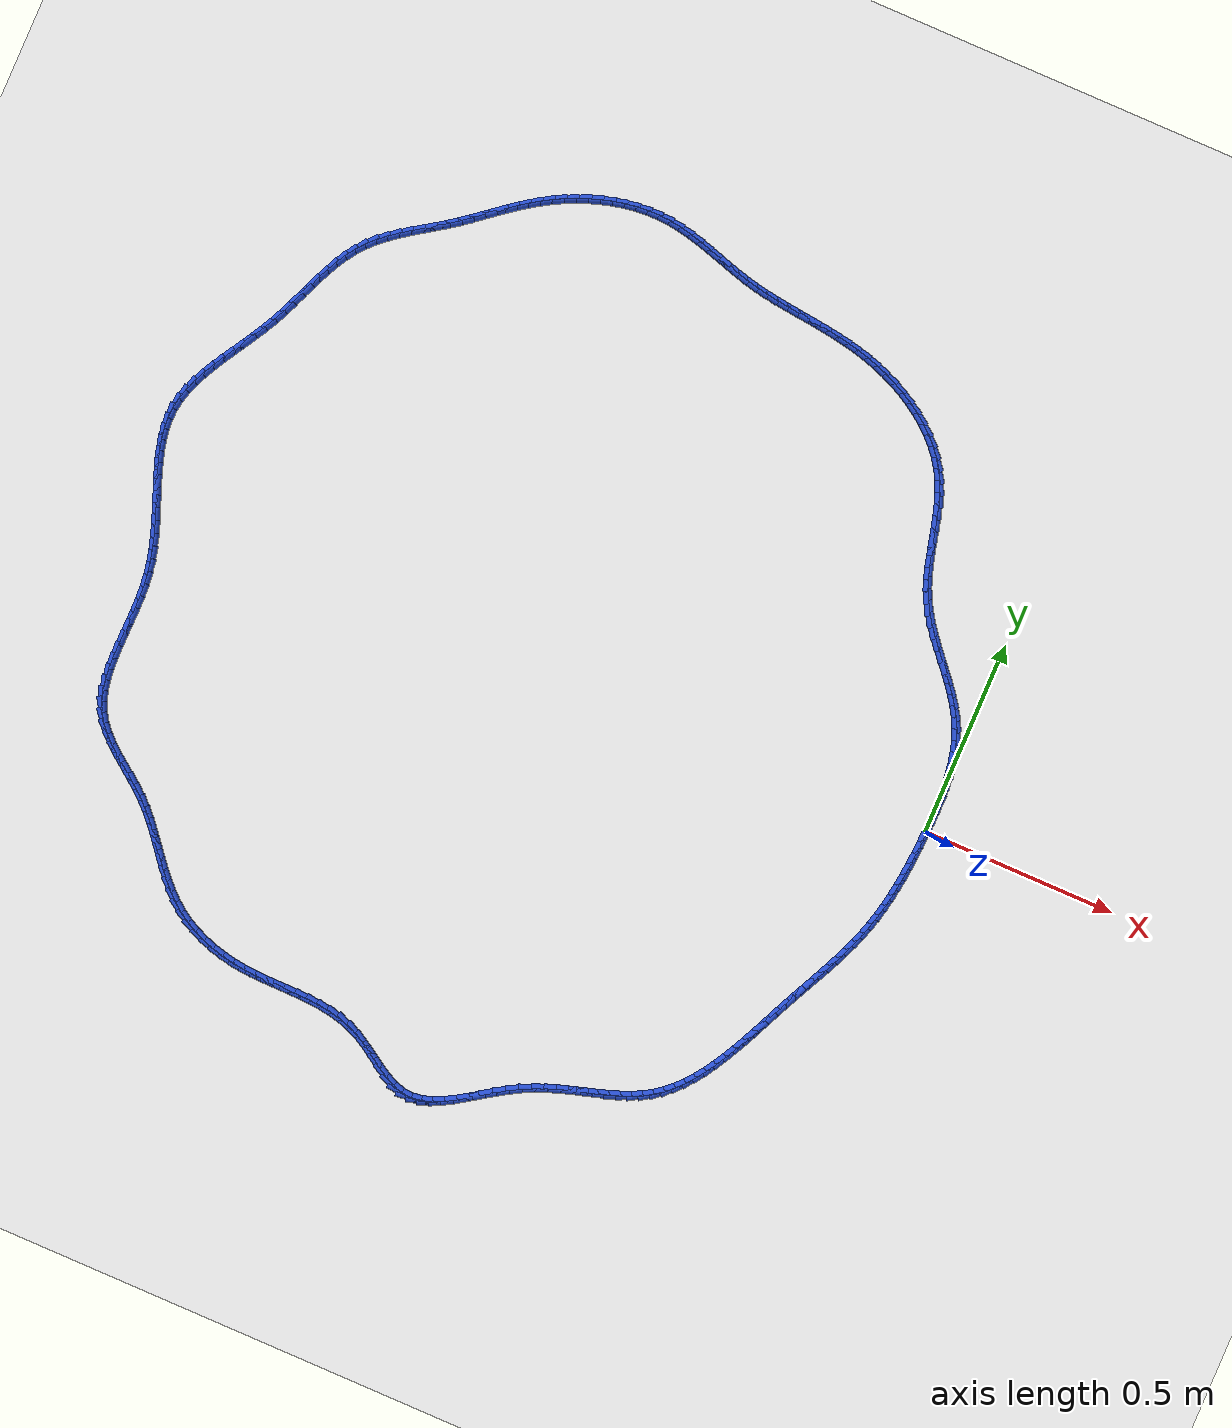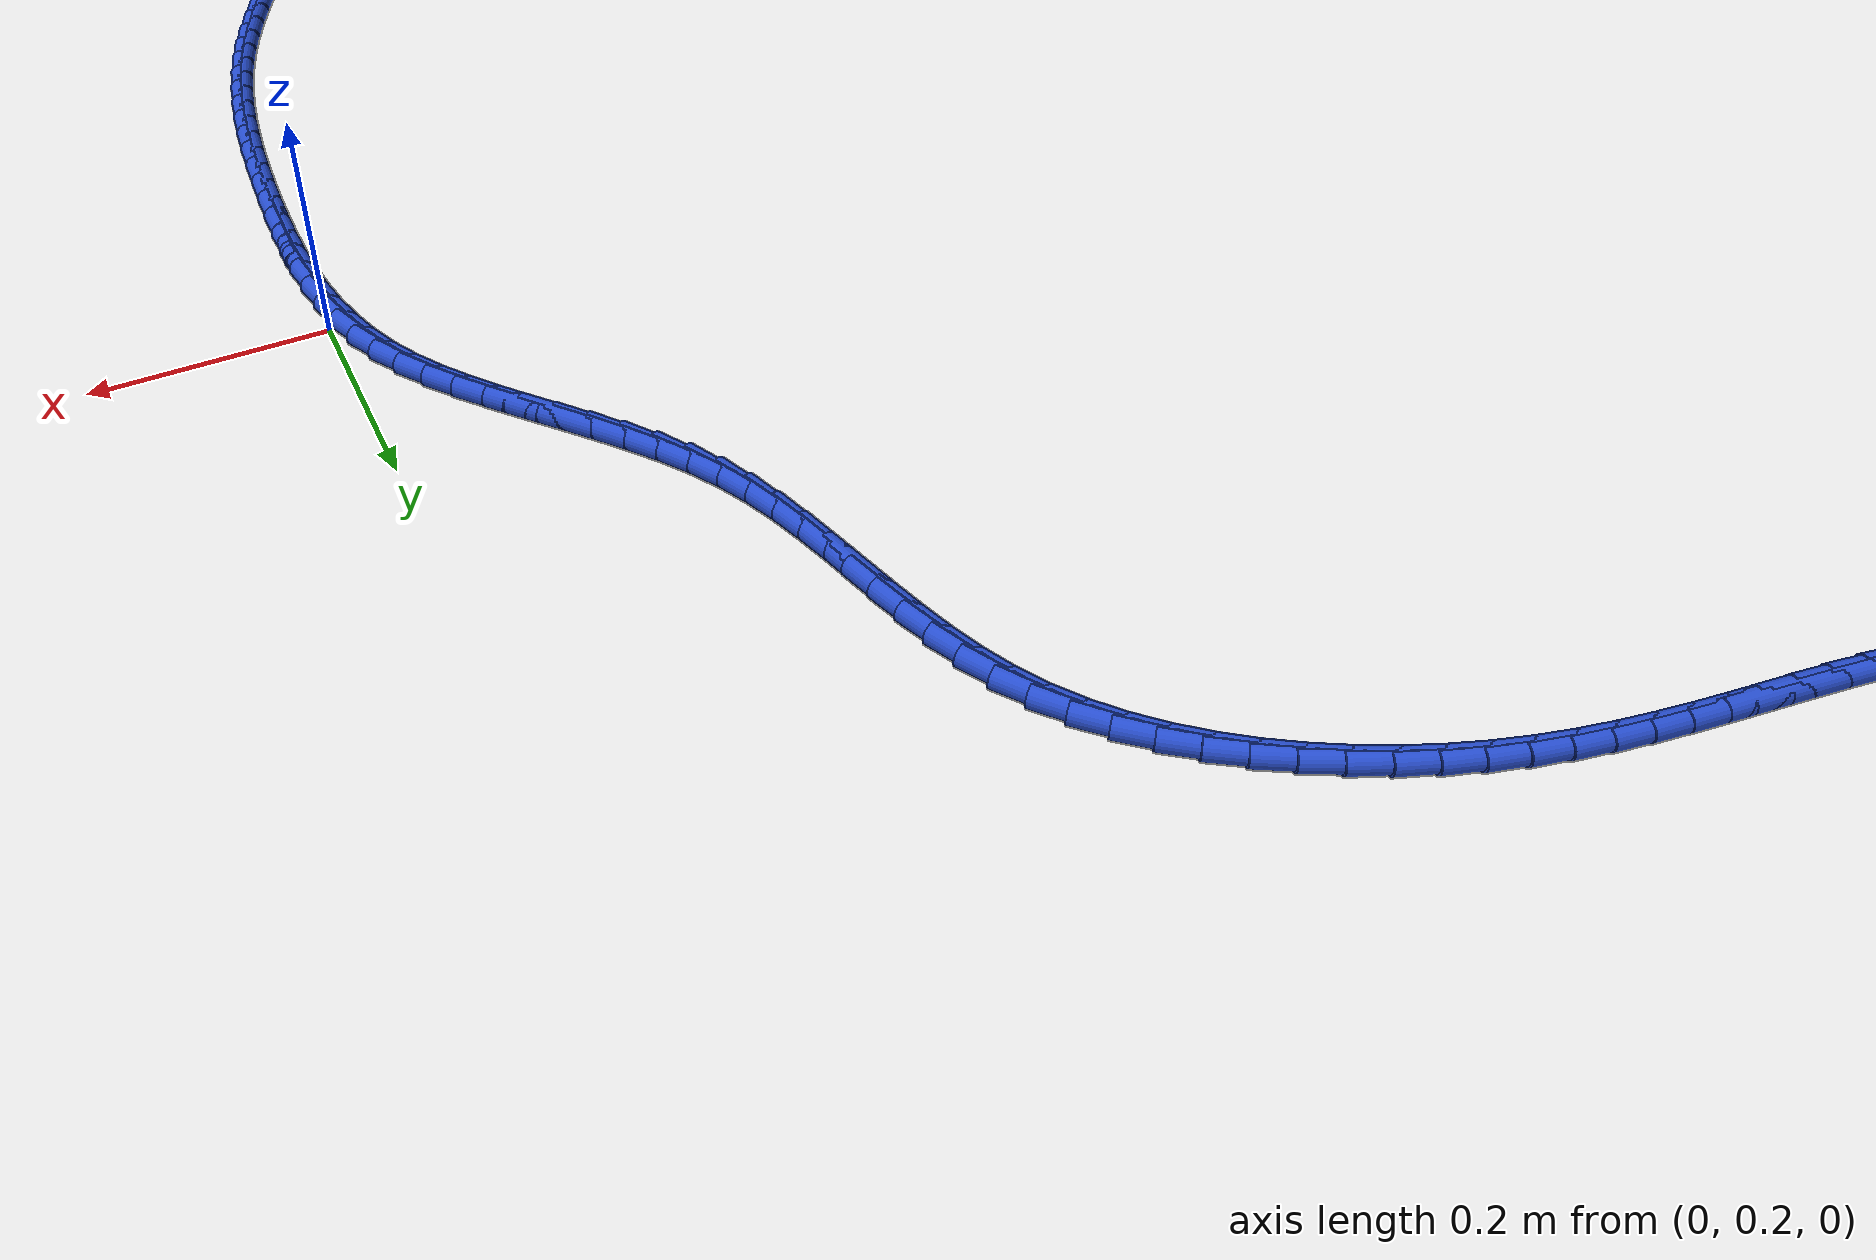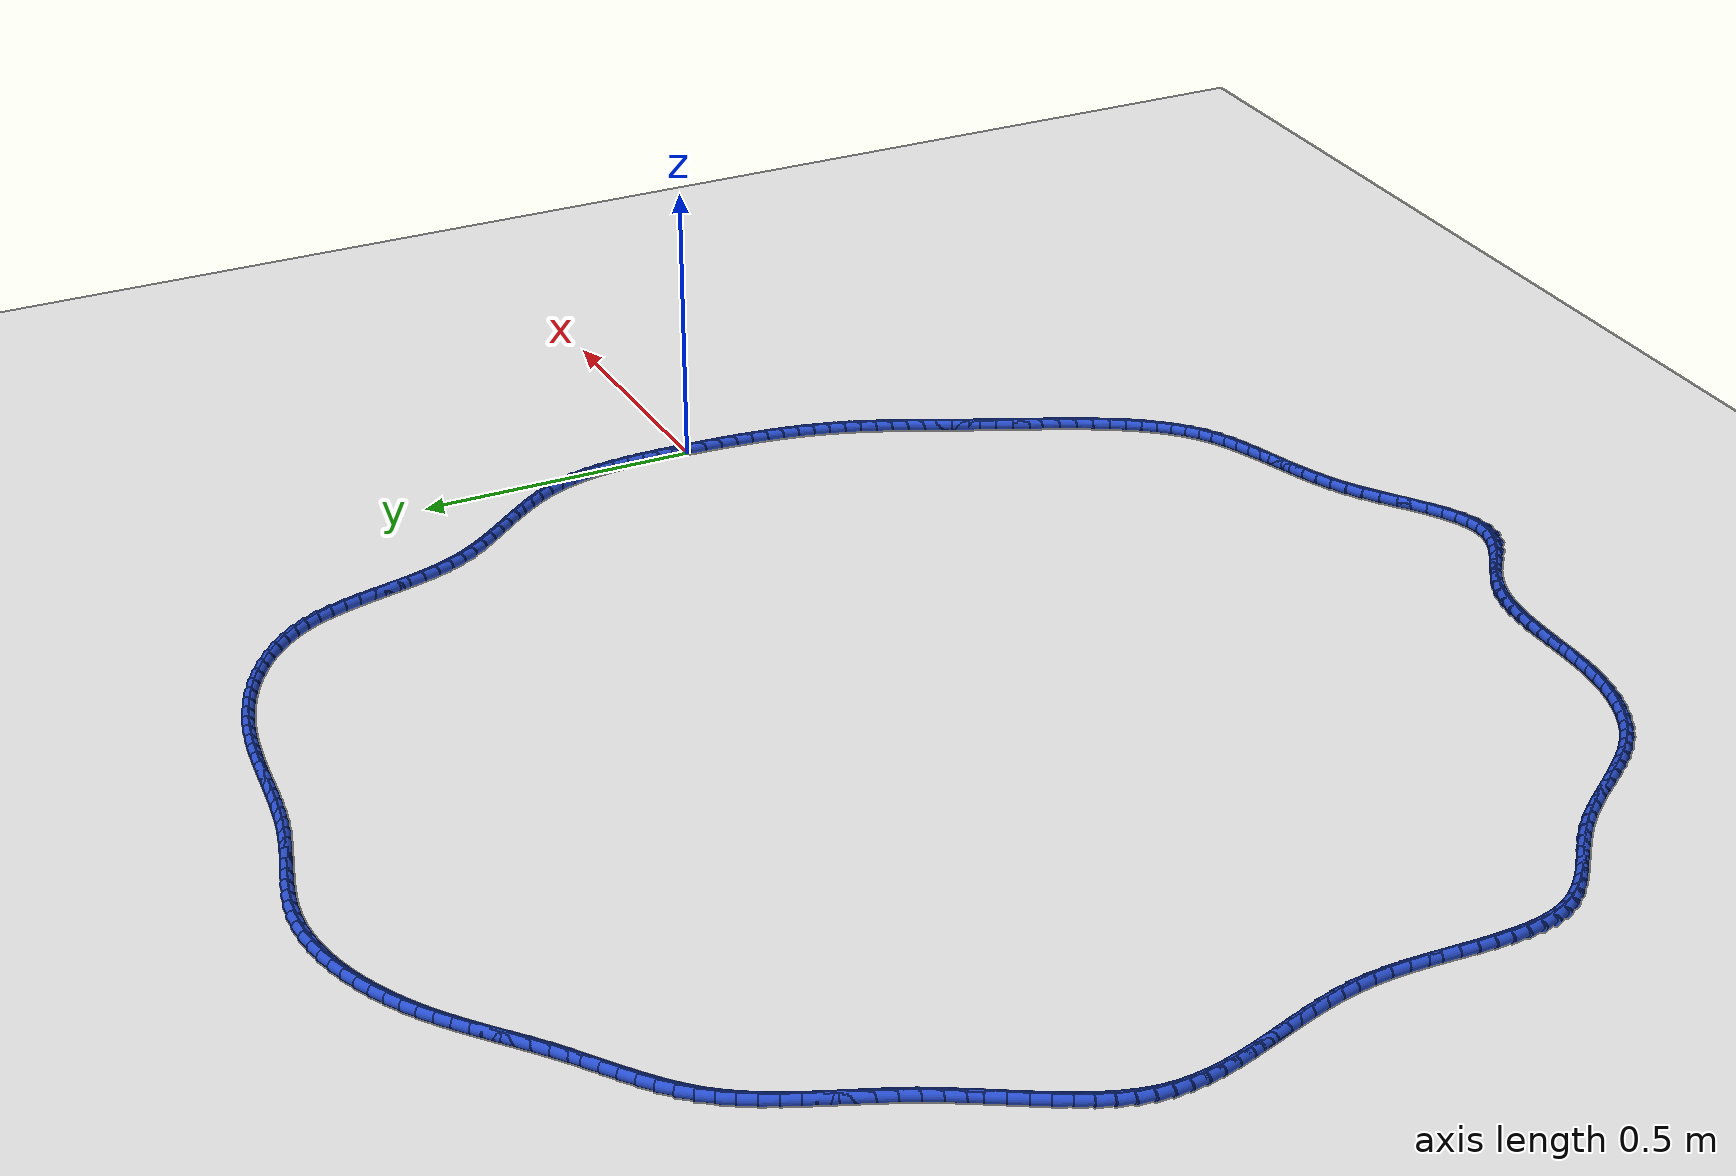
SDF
<sdf version="1.6">
 <world name="default">
  <light name="sun" type="directional">
   <pose>0 0 10 0 -0 0</pose>
   <diffuse>0.8 0.8 0.8 1</diffuse>
   <specular>0.2 0.2 0.2 1</specular>
   <attenuation>
    <range>1000</range>
    <constant>0.9</constant>
    <linear>0.01</linear>
    <quadratic>0.001</quadratic>
   </attenuation>
   <direction>-0.5 0.1 -0.9</direction>
  </light>
  <model name="ground_plane">
   <static>1</static>
   <link name="link">
    <collision name="collision">
     <geometry><plane><normal>0 0 1</normal><size>100 100</size></plane></geometry>
     <surface><friction><ode><mu>100</mu><mu2>50</mu2></ode></friction></surface>
    </collision>
    <visual name="visual">
     <cast_shadows>0</cast_shadows>
     <geometry><plane><normal>0 0 1</normal><size>100 100</size></plane></geometry>
     <material>
      <script><uri>file://media/materials/scripts/gazebo.material</uri><name>Gazebo/WhiteGlow</name></script>
     </material>
    </visual>
   </link>
  </model>
  <gravity>0 0 -9.8</gravity>
  <magnetic_field>6e-06 2.3e-05 -4.2e-05</magnetic_field>
  <atmosphere type="adiabatic"/>
  <physics name="default_physics" default="0" type="ode">
   <max_step_size>0.001</max_step_size>
   <real_time_factor>1</real_time_factor>
   <real_time_update_rate>1000</real_time_update_rate>
  </physics>
  <scene><ambient>0.4 0.4 0.4 1</ambient><background>0.7 0.7 0.7 1</background><shadows>1</shadows></scene>
  <spherical_coordinates>
   <surface_model>EARTH_WGS84</surface_model>
   <latitude_deg>0</latitude_deg>
   <longitude_deg>0</longitude_deg>
   <elevation>0</elevation>
   <heading_deg>0</heading_deg>
  </spherical_coordinates>
  <model name="line">
   <link name="link_0">
    <pose>-1.6642503347652493e-17 -5.551115123125783e-17 0.01 0 1.57 1.5445201447881862</pose>
    <collision name="collision">
     <geometry><cylinder><radius>0.01</radius><length>0.08</length></cylinder></geometry>
    </collision>
    <visual name="visual">
     <material>
      <script><name>Gazebo/Blue</name><uri>file://media/materials/scripts/gazebo.material</uri></script>
     </material>
     <geometry><cylinder><radius>0.01</radius><length>0.08</length></cylinder></geometry>
    </visual>
   </link>
   <link name="link_1">
    <pose>0.0008000069917393401 0.030439082234995526 0.01 0 1.57 1.5642314247843212</pose>
    <collision name="collision">
     <geometry><cylinder><radius>0.01</radius><length>0.08</length></cylinder></geometry>
    </collision>
    <visual name="visual">
     <material>
      <script><name>Gazebo/Blue</name><uri>file://media/materials/scripts/gazebo.material</uri></script>
     </material>
     <geometry><cylinder><radius>0.01</radius><length>0.08</length></cylinder></geometry>
    </visual>
   </link>
   <link name="link_2">
    <pose>0.001000080856398267 0.06091493550307784 0.01 0 1.57 -1.5499489502163104</pose>
    <collision name="collision">
     <geometry><cylinder><radius>0.01</radius><length>0.08</length></cylinder></geometry>
    </collision>
    <visual name="visual">
     <material>
      <script><name>Gazebo/Blue</name><uri>file://media/materials/scripts/gazebo.material</uri></script>
     </material>
     <geometry><cylinder><radius>0.01</radius><length>0.08</length></cylinder></geometry>
    </visual>
   </link>
   <link name="link_3">
    <pose>0.0003668940376574104 0.091283029218157 0.01 0 1.57 -1.5144148475372459</pose>
    <collision name="collision">
     <geometry><cylinder><radius>0.01</radius><length>0.08</length></cylinder></geometry>
    </collision>
    <visual name="visual">
     <material>
      <script><name>Gazebo/Blue</name><uri>file://media/materials/scripts/gazebo.material</uri></script>
     </material>
     <geometry><cylinder><radius>0.01</radius><length>0.08</length></cylinder></geometry>
    </visual>
   </link>
   <link name="link_4">
    <pose>-0.0013328810208025812 0.12139883279414306 0.01 0 1.57 -1.4702018404659567</pose>
    <collision name="collision">
     <geometry><cylinder><radius>0.01</radius><length>0.08</length></cylinder></geometry>
    </collision>
    <visual name="visual">
     <material>
      <script><name>Gazebo/Blue</name><uri>file://media/materials/scripts/gazebo.material</uri></script>
     </material>
     <geometry><cylinder><radius>0.01</radius><length>0.08</length></cylinder></geometry>
    </visual>
   </link>
   <link name="link_5">
    <pose>-0.004332571875301063 0.15111781564494606 0.01 0 1.57 -1.4166719264230967</pose>
    <collision name="collision">
     <geometry><cylinder><radius>0.01</radius><length>0.08</length></cylinder></geometry>
    </collision>
    <visual name="visual">
     <material>
      <script><name>Gazebo/Blue</name><uri>file://media/materials/scripts/gazebo.material</uri></script>
     </material>
     <geometry><cylinder><radius>0.01</radius><length>0.08</length></cylinder></geometry>
    </visual>
   </link>
   <link name="link_6">
    <pose>-0.00886550608215739 0.1802954471844761 0.01 0 1.57 -1.3531977401613675</pose>
    <collision name="collision">
     <geometry><cylinder><radius>0.01</radius><length>0.08</length></cylinder></geometry>
    </collision>
    <visual name="visual">
     <material>
      <script><name>Gazebo/Blue</name><uri>file://media/materials/scripts/gazebo.material</uri></script>
     </material>
     <geometry><cylinder><radius>0.01</radius><length>0.08</length></cylinder></geometry>
    </visual>
   </link>
   <link name="link_7">
    <pose>-0.015165011197690913 0.20878719682664318 0.01 0 1.57 -1.279306285404666</pose>
    <collision name="collision">
     <geometry><cylinder><radius>0.01</radius><length>0.08</length></cylinder></geometry>
    </collision>
    <visual name="visual">
     <material>
      <script><name>Gazebo/Blue</name><uri>file://media/materials/scripts/gazebo.material</uri></script>
     </material>
     <geometry><cylinder><radius>0.01</radius><length>0.08</length></cylinder></geometry>
    </visual>
   </link>
   <link name="link_8">
    <pose>-0.023464414778220987 0.23644853398535742 0.01 0 1.57 -1.1948831399953643</pose>
    <collision name="collision">
     <geometry><cylinder><radius>0.01</radius><length>0.08</length></cylinder></geometry>
    </collision>
    <visual name="visual">
     <material>
      <script><name>Gazebo/Blue</name><uri>file://media/materials/scripts/gazebo.material</uri></script>
     </material>
     <geometry><cylinder><radius>0.01</radius><length>0.08</length></cylinder></geometry>
    </visual>
   </link>
   <link name="link_9">
    <pose>-0.03399704438006697 0.2631349280745289 0.01 0 1.57 -1.1022734935256397</pose>
    <collision name="collision">
     <geometry><cylinder><radius>0.01</radius><length>0.08</length></cylinder></geometry>
    </collision>
    <visual name="visual">
     <material>
      <script><name>Gazebo/Blue</name><uri>file://media/materials/scripts/gazebo.material</uri></script>
     </material>
     <geometry><cylinder><radius>0.01</radius><length>0.08</length></cylinder></geometry>
    </visual>
   </link>
   <link name="link_10">
    <pose>-0.04694926712609044 0.28872669489334557 0.01 0 1.57 -1.0190361585610097</pose>
    <collision name="collision">
     <geometry><cylinder><radius>0.01</radius><length>0.08</length></cylinder></geometry>
    </collision>
    <visual name="visual">
     <material>
      <script><name>Gazebo/Blue</name><uri>file://media/materials/scripts/gazebo.material</uri></script>
     </material>
     <geometry><cylinder><radius>0.01</radius><length>0.08</length></cylinder></geometry>
    </visual>
   </link>
   <link name="link_11">
    <pose>-0.062090200094298234 0.3133249138628029 0.01 0 1.57 -0.9543095627153845</pose>
    <collision name="collision">
     <geometry><cylinder><radius>0.01</radius><length>0.08</length></cylinder></geometry>
    </collision>
    <visual name="visual">
     <material>
      <script><name>Gazebo/Blue</name><uri>file://media/materials/scripts/gazebo.material</uri></script>
     </material>
     <geometry><cylinder><radius>0.01</radius><length>0.08</length></cylinder></geometry>
    </visual>
   </link>
   <link name="link_12">
    <pose>-0.07897045504207179 0.33714627380061163 0.01 0 1.57 -0.9077355483012163</pose>
    <collision name="collision">
     <geometry><cylinder><radius>0.01</radius><length>0.08</length></cylinder></geometry>
    </collision>
    <visual name="visual">
     <material>
      <script><name>Gazebo/Blue</name><uri>file://media/materials/scripts/gazebo.material</uri></script>
     </material>
     <geometry><cylinder><radius>0.01</radius><length>0.08</length></cylinder></geometry>
    </visual>
   </link>
   <link name="link_13">
    <pose>-0.09713872558459881 0.3604084783979937 0.01 0 1.57 -0.8785258489261263</pose>
    <collision name="collision">
     <geometry><cylinder><radius>0.01</radius><length>0.08</length></cylinder></geometry>
    </collision>
    <visual name="visual">
     <material>
      <script><name>Gazebo/Blue</name><uri>file://media/materials/scripts/gazebo.material</uri></script>
     </material>
     <geometry><cylinder><radius>0.01</radius><length>0.08</length></cylinder></geometry>
    </visual>
   </link>
   <link name="link_14">
    <pose>-0.11614370533706699 0.38332923134617064 0.01 0 1.57 -0.8659731199736854</pose>
    <collision name="collision">
     <geometry><cylinder><radius>0.01</radius><length>0.08</length></cylinder></geometry>
    </collision>
    <visual name="visual">
     <material>
      <script><name>Gazebo/Blue</name><uri>file://media/materials/scripts/gazebo.material</uri></script>
     </material>
     <geometry><cylinder><radius>0.01</radius><length>0.08</length></cylinder></geometry>
    </visual>
   </link>
   <link name="link_15">
    <pose>-0.13553408791466404 0.4061262363363642 0.01 0 1.57 -0.8696808996757444</pose>
    <collision name="collision">
     <geometry><cylinder><radius>0.01</radius><length>0.08</length></cylinder></geometry>
    </collision>
    <visual name="visual">
     <material>
      <script><name>Gazebo/Blue</name><uri>file://media/materials/scripts/gazebo.material</uri></script>
     </material>
     <geometry><cylinder><radius>0.01</radius><length>0.08</length></cylinder></geometry>
    </visual>
   </link>
   <link name="link_16">
    <pose>-0.15485856693257763 0.4290171970597959 0.01 0 1.57 -0.8896454597032964</pose>
    <collision name="collision">
     <geometry><cylinder><radius>0.01</radius><length>0.08</length></cylinder></geometry>
    </collision>
    <visual name="visual">
     <material>
      <script><name>Gazebo/Blue</name><uri>file://media/materials/scripts/gazebo.material</uri></script>
     </material>
     <geometry><cylinder><radius>0.01</radius><length>0.08</length></cylinder></geometry>
    </visual>
   </link>
   <link name="link_17">
    <pose>-0.17366583600599542 0.4522198172076878 0.01 0 1.57 -0.9262236966206563</pose>
    <collision name="collision">
     <geometry><cylinder><radius>0.01</radius><length>0.08</length></cylinder></geometry>
    </collision>
    <visual name="visual">
     <material>
      <script><name>Gazebo/Blue</name><uri>file://media/materials/scripts/gazebo.material</uri></script>
     </material>
     <geometry><cylinder><radius>0.01</radius><length>0.08</length></cylinder></geometry>
    </visual>
   </link>
   <link name="link_18">
    <pose>-0.19150458875010512 0.47595180047126134 0.01 0 1.57 -0.9799831927021702</pose>
    <collision name="collision">
     <geometry><cylinder><radius>0.01</radius><length>0.08</length></cylinder></geometry>
    </collision>
    <visual name="visual">
     <material>
      <script><name>Gazebo/Blue</name><uri>file://media/materials/scripts/gazebo.material</uri></script>
     </material>
     <geometry><cylinder><radius>0.01</radius><length>0.08</length></cylinder></geometry>
    </visual>
   </link>
   <link name="link_19">
    <pose>-0.20792351878009438 0.5004308505417382 0.01 0 1.57 -1.051399155599642</pose>
    <collision name="collision">
     <geometry><cylinder><radius>0.01</radius><length>0.08</length></cylinder></geometry>
    </collision>
    <visual name="visual">
     <material>
      <script><name>Gazebo/Blue</name><uri>file://media/materials/scripts/gazebo.material</uri></script>
     </material>
     <geometry><cylinder><radius>0.01</radius><length>0.08</length></cylinder></geometry>
    </visual>
   </link>
   <link name="link_20">
    <pose>-0.22247131971115094 0.52587467111034 0.01 0 1.57 -1.1357771198597164</pose>
    <collision name="collision">
     <geometry><cylinder><radius>0.01</radius><length>0.08</length></cylinder></geometry>
    </collision>
    <visual name="visual">
     <material>
      <script><name>Gazebo/Blue</name><uri>file://media/materials/scripts/gazebo.material</uri></script>
     </material>
     <geometry><cylinder><radius>0.01</radius><length>0.08</length></cylinder></geometry>
    </visual>
   </link>
   <link name="link_21">
    <pose>-0.23481664504538222 0.5524403254533082 0.01 0 1.57 -1.2091313294210193</pose>
    <collision name="collision">
     <geometry><cylinder><radius>0.01</radius><length>0.08</length></cylinder></geometry>
    </collision>
    <visual name="visual">
     <material>
      <script><name>Gazebo/Blue</name><uri>file://media/materials/scripts/gazebo.material</uri></script>
     </material>
     <geometry><cylinder><radius>0.01</radius><length>0.08</length></cylinder></geometry>
    </visual>
   </link>
   <link name="link_22">
    <pose>-0.2452344332365281 0.5799783963057 0.01 0 1.57 -1.263931293792359</pose>
    <collision name="collision">
     <geometry><cylinder><radius>0.01</radius><length>0.08</length></cylinder></geometry>
    </collision>
    <visual name="visual">
     <material>
      <script><name>Gazebo/Blue</name><uri>file://media/materials/scripts/gazebo.material</uri></script>
     </material>
     <geometry><cylinder><radius>0.01</radius><length>0.08</length></cylinder></geometry>
    </visual>
   </link>
   <link name="link_23">
    <pose>-0.25419071796160425 0.6082428666646291 0.01 0 1.57 -1.3006178087018954</pose>
    <collision name="collision">
     <geometry><cylinder><radius>0.01</radius><length>0.08</length></cylinder></geometry>
    </collision>
    <visual name="visual">
     <material>
      <script><name>Gazebo/Blue</name><uri>file://media/materials/scripts/gazebo.material</uri></script>
     </material>
     <geometry><cylinder><radius>0.01</radius><length>0.08</length></cylinder></geometry>
    </visual>
   </link>
   <link name="link_24">
    <pose>-0.26215160461107295 0.6369876832756477 0.01 0 1.57 -1.3197595442775536</pose>
    <collision name="collision">
     <geometry><cylinder><radius>0.01</radius><length>0.08</length></cylinder></geometry>
    </collision>
    <visual name="visual">
     <material>
      <script><name>Gazebo/Blue</name><uri>file://media/materials/scripts/gazebo.material</uri></script>
     </material>
     <geometry><cylinder><radius>0.01</radius><length>0.08</length></cylinder></geometry>
    </visual>
   </link>
   <link name="link_25">
    <pose>-0.26958319857539687 0.6659667928843084 0.01 0 1.57 -1.3217095534787657</pose>
    <collision name="collision">
     <geometry><cylinder><radius>0.01</radius><length>0.08</length></cylinder></geometry>
    </collision>
    <visual name="visual">
     <material>
      <script><name>Gazebo/Blue</name><uri>file://media/materials/scripts/gazebo.material</uri></script>
     </material>
     <geometry><cylinder><radius>0.01</radius><length>0.08</length></cylinder></geometry>
    </visual>
   </link>
   <link name="link_26">
    <pose>-0.27695160524503804 0.6949341422361632 0.01 0 1.57 -1.3064434179974773</pose>
    <collision name="collision">
     <geometry><cylinder><radius>0.01</radius><length>0.08</length></cylinder></geometry>
    </collision>
    <visual name="visual">
     <material>
      <script><name>Gazebo/Blue</name><uri>file://media/materials/scripts/gazebo.material</uri></script>
     </material>
     <geometry><cylinder><radius>0.01</radius><length>0.08</length></cylinder></geometry>
    </visual>
   </link>
   <link name="link_27">
    <pose>-0.2847229300104592 0.7236436780767651 0.01 0 1.57 -1.2735389336065988</pose>
    <collision name="collision">
     <geometry><cylinder><radius>0.01</radius><length>0.08</length></cylinder></geometry>
    </collision>
    <visual name="visual">
     <material>
      <script><name>Gazebo/Blue</name><uri>file://media/materials/scripts/gazebo.material</uri></script>
     </material>
     <geometry><cylinder><radius>0.01</radius><length>0.08</length></cylinder></geometry>
    </visual>
   </link>
   <link name="link_28">
    <pose>-0.29336327826212233 0.7518493471516657 0.01 0 1.57 -1.2222965829232277</pose>
    <collision name="collision">
     <geometry><cylinder><radius>0.01</radius><length>0.08</length></cylinder></geometry>
    </collision>
    <visual name="visual">
     <material>
      <script><name>Gazebo/Blue</name><uri>file://media/materials/scripts/gazebo.material</uri></script>
     </material>
     <geometry><cylinder><radius>0.01</radius><length>0.08</length></cylinder></geometry>
    </visual>
   </link>
   <link name="link_29">
    <pose>-0.3033387553904901 0.7793050962064177 0.01 0 1.57 -1.1520415776940556</pose>
    <collision name="collision">
     <geometry><cylinder><radius>0.01</radius><length>0.08</length></cylinder></geometry>
    </collision>
    <visual name="visual">
     <material>
      <script><name>Gazebo/Blue</name><uri>file://media/materials/scripts/gazebo.material</uri></script>
     </material>
     <geometry><cylinder><radius>0.01</radius><length>0.08</length></cylinder></geometry>
    </visual>
   </link>
   <link name="link_30">
    <pose>-0.31511546678602487 0.8057648719865738 0.01 0 1.57 -1.0628116432189374</pose>
    <collision name="collision">
     <geometry><cylinder><radius>0.01</radius><length>0.08</length></cylinder></geometry>
    </collision>
    <visual name="visual">
     <material>
      <script><name>Gazebo/Blue</name><uri>file://media/materials/scripts/gazebo.material</uri></script>
     </material>
     <geometry><cylinder><radius>0.01</radius><length>0.08</length></cylinder></geometry>
    </visual>
   </link>
   <link name="link_31">
    <pose>-0.32915535796203527 0.8309840066204499 0.01 0 1.57 -0.9646996621314903</pose>
    <collision name="collision">
     <geometry><cylinder><radius>0.01</radius><length>0.08</length></cylinder></geometry>
    </collision>
    <visual name="visual">
     <material>
      <script><name>Gazebo/Blue</name><uri>file://media/materials/scripts/gazebo.material</uri></script>
     </material>
     <geometry><cylinder><radius>0.01</radius><length>0.08</length></cylinder></geometry>
    </visual>
   </link>
   <link name="link_32">
    <pose>-0.34566484152624843 0.8548029335193719 0.01 0 1.57 -0.872752068725949</pose>
    <collision name="collision">
     <geometry><cylinder><radius>0.01</radius><length>0.08</length></cylinder></geometry>
    </collision>
    <visual name="visual">
     <material>
      <script><name>Gazebo/Blue</name><uri>file://media/materials/scripts/gazebo.material</uri></script>
     </material>
     <geometry><cylinder><radius>0.01</radius><length>0.08</length></cylinder></geometry>
    </visual>
   </link>
   <link name="link_33">
    <pose>-0.36445080013086184 0.8771951433685966 0.01 0 1.57 -0.7881748281781484</pose>
    <collision name="collision">
     <geometry><cylinder><radius>0.01</radius><length>0.08</length></cylinder></geometry>
    </collision>
    <visual name="visual">
     <material>
      <script><name>Gazebo/Blue</name><uri>file://media/materials/scripts/gazebo.material</uri></script>
     </material>
     <geometry><cylinder><radius>0.01</radius><length>0.08</length></cylinder></geometry>
    </visual>
   </link>
   <link name="link_34">
    <pose>-0.3852853413779471 0.8981457081461137 0.01 0 1.57 -0.7105371816020005</pose>
    <collision name="collision">
     <geometry><cylinder><radius>0.01</radius><length>0.08</length></cylinder></geometry>
    </collision>
    <visual name="visual">
     <material>
      <script><name>Gazebo/Blue</name><uri>file://media/materials/scripts/gazebo.material</uri></script>
     </material>
     <geometry><cylinder><radius>0.01</radius><length>0.08</length></cylinder></geometry>
    </visual>
   </link>
   <link name="link_35">
    <pose>-0.4079405728695761 0.9176396998299137 0.01 0 1.57 -0.63917088614371</pose>
    <collision name="collision">
     <geometry><cylinder><radius>0.01</radius><length>0.08</length></cylinder></geometry>
    </collision>
    <visual name="visual">
     <material>
      <script><name>Gazebo/Blue</name><uri>file://media/materials/scripts/gazebo.material</uri></script>
     </material>
     <geometry><cylinder><radius>0.01</radius><length>0.08</length></cylinder></geometry>
    </visual>
   </link>
   <link name="link_36">
    <pose>-0.43218860220782035 0.9356621903979863 0.01 0 1.57 -0.5732855182751896</pose>
    <collision name="collision">
     <geometry><cylinder><radius>0.01</radius><length>0.08</length></cylinder></geometry>
    </collision>
    <visual name="visual">
     <material>
      <script><name>Gazebo/Blue</name><uri>file://media/materials/scripts/gazebo.material</uri></script>
     </material>
     <geometry><cylinder><radius>0.01</radius><length>0.08</length></cylinder></geometry>
    </visual>
   </link>
   <link name="link_37">
    <pose>-0.4578015369947518 0.9521982518283214 0.01 0 1.57 -0.5120446028015501</pose>
    <collision name="collision">
     <geometry><cylinder><radius>0.01</radius><length>0.08</length></cylinder></geometry>
    </collision>
    <visual name="visual">
     <material>
      <script><name>Gazebo/Blue</name><uri>file://media/materials/scripts/gazebo.material</uri></script>
     </material>
     <geometry><cylinder><radius>0.01</radius><length>0.08</length></cylinder></geometry>
    </visual>
   </link>
   <link name="link_38">
    <pose>-0.48455148483244176 0.9672329560989088 0.01 0 1.57 -0.4546086128311678</pose>
    <collision name="collision">
     <geometry><cylinder><radius>0.01</radius><length>0.08</length></cylinder></geometry>
    </collision>
    <visual name="visual">
     <material>
      <script><name>Gazebo/Blue</name><uri>file://media/materials/scripts/gazebo.material</uri></script>
     </material>
     <geometry><cylinder><radius>0.01</radius><length>0.08</length></cylinder></geometry>
    </visual>
   </link>
   <link name="link_39">
    <pose>-0.5122105533229622 0.9807513751877388 0.01 0 1.57 -0.40015327292221275</pose>
    <collision name="collision">
     <geometry><cylinder><radius>0.01</radius><length>0.08</length></cylinder></geometry>
    </collision>
    <visual name="visual">
     <material>
      <script><name>Gazebo/Blue</name><uri>file://media/materials/scripts/gazebo.material</uri></script>
     </material>
     <geometry><cylinder><radius>0.01</radius><length>0.08</length></cylinder></geometry>
    </visual>
   </link>
   <link name="link_40">
    <pose>-0.5405508500683848 0.992738581072801 0.01 0 1.57 -0.3478705174542795</pose>
    <collision name="collision">
     <geometry><cylinder><radius>0.01</radius><length>0.08</length></cylinder></geometry>
    </collision>
    <visual name="visual">
     <material>
      <script><name>Gazebo/Blue</name><uri>file://media/materials/scripts/gazebo.material</uri></script>
     </material>
     <geometry><cylinder><radius>0.01</radius><length>0.08</length></cylinder></geometry>
    </visual>
   </link>
   <link name="link_41">
    <pose>-0.5693444826707813 1.0031796457320858 0.01 0 1.57 -0.2969850269026818</pose>
    <collision name="collision">
     <geometry><cylinder><radius>0.01</radius><length>0.08</length></cylinder></geometry>
    </collision>
    <visual name="visual">
     <material>
      <script><name>Gazebo/Blue</name><uri>file://media/materials/scripts/gazebo.material</uri></script>
     </material>
     <geometry><cylinder><radius>0.01</radius><length>0.08</length></cylinder></geometry>
    </visual>
   </link>
   <link name="link_42">
    <pose>-0.5983645521219593 1.0120608272113627 0.01 0 1.57 -0.24893454527413506</pose>
    <collision name="collision">
     <geometry><cylinder><radius>0.01</radius><length>0.08</length></cylinder></geometry>
    </collision>
    <visual name="visual">
     <material>
      <script><name>Gazebo/Blue</name><uri>file://media/materials/scripts/gazebo.material</uri></script>
     </material>
     <geometry><cylinder><radius>0.01</radius><length>0.08</length></cylinder></geometry>
    </visual>
   </link>
   <link name="link_43">
    <pose>-0.6274580510673612 1.0194566072478535 0.01 0 1.57 -0.20743782805276378</pose>
    <collision name="collision">
     <geometry><cylinder><radius>0.01</radius><length>0.08</length></cylinder></geometry>
    </collision>
    <visual name="visual">
     <material>
      <script><name>Gazebo/Blue</name><uri>file://media/materials/scripts/gazebo.material</uri></script>
     </material>
     <geometry><cylinder><radius>0.01</radius><length>0.08</length></cylinder></geometry>
    </visual>
   </link>
   <link name="link_44">
    <pose>-0.6565955764009695 1.0255890461285768 0.01 0 1.57 -0.17329635866732881</pose>
    <collision name="collision">
     <geometry><cylinder><radius>0.01</radius><length>0.08</length></cylinder></geometry>
    </collision>
    <visual name="visual">
     <material>
      <script><name>Gazebo/Blue</name><uri>file://media/materials/scripts/gazebo.material</uri></script>
     </material>
     <geometry><cylinder><radius>0.01</radius><length>0.08</length></cylinder></geometry>
    </visual>
   </link>
   <link name="link_45">
    <pose>-0.6857594935516883 1.0306942553025245 0.01 0 1.57 -0.14681715773072526</pose>
    <collision name="collision">
     <geometry><cylinder><radius>0.01</radius><length>0.08</length></cylinder></geometry>
    </collision>
    <visual name="visual">
     <material>
      <script><name>Gazebo/Blue</name><uri>file://media/materials/scripts/gazebo.material</uri></script>
     </material>
     <geometry><cylinder><radius>0.01</radius><length>0.08</length></cylinder></geometry>
    </visual>
   </link>
   <link name="link_46">
    <pose>-0.7149321679484211 1.0350083462186883 0.01 0 1.57 -0.12818877107740248</pose>
    <collision name="collision">
     <geometry><cylinder><radius>0.01</radius><length>0.08</length></cylinder></geometry>
    </collision>
    <visual name="visual">
     <material>
      <script><name>Gazebo/Blue</name><uri>file://media/materials/scripts/gazebo.material</uri></script>
     </material>
     <geometry><cylinder><radius>0.01</radius><length>0.08</length></cylinder></geometry>
    </visual>
   </link>
   <link name="link_47">
    <pose>-0.7440959650200716 1.038767430326061 0.01 0 1.57 -0.11752418151627553</pose>
    <collision name="collision">
     <geometry><cylinder><radius>0.01</radius><length>0.08</length></cylinder></geometry>
    </collision>
    <visual name="visual">
     <material>
      <script><name>Gazebo/Blue</name><uri>file://media/materials/scripts/gazebo.material</uri></script>
     </material>
     <geometry><cylinder><radius>0.01</radius><length>0.08</length></cylinder></geometry>
    </visual>
   </link>
   <link name="link_48">
    <pose>-0.7732332501955433 1.0422076190736334 0.01 0 1.57 -0.11489370879194383</pose>
    <collision name="collision">
     <geometry><cylinder><radius>0.01</radius><length>0.08</length></cylinder></geometry>
    </collision>
    <visual name="visual">
     <material>
      <script><name>Gazebo/Blue</name><uri>file://media/materials/scripts/gazebo.material</uri></script>
     </material>
     <geometry><cylinder><radius>0.01</radius><length>0.08</length></cylinder></geometry>
    </visual>
   </link>
   <link name="link_49">
    <pose>-0.80232638890374 1.045565023910398 0.01 0 1.57 -0.12034461445732512</pose>
    <collision name="collision">
     <geometry><cylinder><radius>0.01</radius><length>0.08</length></cylinder></geometry>
    </collision>
    <visual name="visual">
     <material>
      <script><name>Gazebo/Blue</name><uri>file://media/materials/scripts/gazebo.material</uri></script>
     </material>
     <geometry><cylinder><radius>0.01</radius><length>0.08</length></cylinder></geometry>
    </visual>
   </link>
   <link name="link_50">
    <pose>-0.8313577465735656 1.049075756285347 0.01 0 1.57 -0.13390578188499033</pose>
    <collision name="collision">
     <geometry><cylinder><radius>0.01</radius><length>0.08</length></cylinder></geometry>
    </collision>
    <visual name="visual">
     <material>
      <script><name>Gazebo/Blue</name><uri>file://media/materials/scripts/gazebo.material</uri></script>
     </material>
     <geometry><cylinder><radius>0.01</radius><length>0.08</length></cylinder></geometry>
    </visual>
   </link>
   <link name="link_51">
    <pose>-0.8603096886339238 1.0529759276474722 0.01 0 1.57 -0.1555767067208262</pose>
    <collision name="collision">
     <geometry><cylinder><radius>0.01</radius><length>0.08</length></cylinder></geometry>
    </collision>
    <visual name="visual">
     <material>
      <script><name>Gazebo/Blue</name><uri>file://media/materials/scripts/gazebo.material</uri></script>
     </material>
     <geometry><cylinder><radius>0.01</radius><length>0.08</length></cylinder></geometry>
    </visual>
   </link>
   <link name="link_52">
    <pose>-0.8891645805137176 1.0575016494457647 0.01 0 1.57 -0.18530071850197205</pose>
    <collision name="collision">
     <geometry><cylinder><radius>0.01</radius><length>0.08</length></cylinder></geometry>
    </collision>
    <visual name="visual">
     <material>
      <script><name>Gazebo/Blue</name><uri>file://media/materials/scripts/gazebo.material</uri></script>
     </material>
     <geometry><cylinder><radius>0.01</radius><length>0.08</length></cylinder></geometry>
    </visual>
   </link>
   <link name="link_53">
    <pose>-0.9179047876418517 1.0628890331292178 0.01 0 1.57 -0.22275290566603131</pose>
    <collision name="collision">
     <geometry><cylinder><radius>0.01</radius><length>0.08</length></cylinder></geometry>
    </collision>
    <visual name="visual">
     <material>
      <script><name>Gazebo/Blue</name><uri>file://media/materials/scripts/gazebo.material</uri></script>
     </material>
     <geometry><cylinder><radius>0.01</radius><length>0.08</length></cylinder></geometry>
    </visual>
   </link>
   <link name="link_54">
    <pose>-0.9465131996557178 1.0693691753389878 0.01 0 1.57 -0.25923176158261857</pose>
    <collision name="collision">
     <geometry><cylinder><radius>0.01</radius><length>0.08</length></cylinder></geometry>
    </collision>
    <visual name="visual">
     <material>
      <script><name>Gazebo/Blue</name><uri>file://media/materials/scripts/gazebo.material</uri></script>
     </material>
     <geometry><cylinder><radius>0.01</radius><length>0.08</length></cylinder></geometry>
    </visual>
   </link>
   <link name="link_55">
    <pose>-0.974998801717022 1.0769235315094605 0.01 0 1.57 -0.28262273843052116</pose>
    <collision name="collision">
     <geometry><cylinder><radius>0.01</radius><length>0.08</length></cylinder></geometry>
    </collision>
    <visual name="visual">
     <material>
      <script><name>Gazebo/Blue</name><uri>file://media/materials/scripts/gazebo.material</uri></script>
     </material>
     <geometry><cylinder><radius>0.01</radius><length>0.08</length></cylinder></geometry>
    </visual>
   </link>
   <link name="link_56">
    <pose>-1.00340821507115 1.0851735138263947 0.01 0 1.57 -0.29223755716707067</pose>
    <collision name="collision">
     <geometry><cylinder><radius>0.01</radius><length>0.08</length></cylinder></geometry>
    </collision>
    <visual name="visual">
     <material>
      <script><name>Gazebo/Blue</name><uri>file://media/materials/scripts/gazebo.material</uri></script>
     </material>
     <geometry><cylinder><radius>0.01</radius><length>0.08</length></cylinder></geometry>
    </visual>
   </link>
   <link name="link_57">
    <pose>-1.031790990753054 1.093712506826285 0.01 0 1.57 -0.28821362235391973</pose>
    <collision name="collision">
     <geometry><cylinder><radius>0.01</radius><length>0.08</length></cylinder></geometry>
    </collision>
    <visual name="visual">
     <material>
      <script><name>Gazebo/Blue</name><uri>file://media/materials/scripts/gazebo.material</uri></script>
     </material>
     <geometry><cylinder><radius>0.01</radius><length>0.08</length></cylinder></geometry>
    </visual>
   </link>
   <link name="link_58">
    <pose>-1.0601966797976858 1.1021338950456256 0.01 0 1.57 -0.27050898241524346</pose>
    <collision name="collision">
     <geometry><cylinder><radius>0.01</radius><length>0.08</length></cylinder></geometry>
    </collision>
    <visual name="visual">
     <material>
      <script><name>Gazebo/Blue</name><uri>file://media/materials/scripts/gazebo.material</uri></script>
     </material>
     <geometry><cylinder><radius>0.01</radius><length>0.08</length></cylinder></geometry>
    </visual>
   </link>
   <link name="link_59">
    <pose>-1.088674833239998 1.1100310630209114 0.01 0 1.57 -0.23892404549896074</pose>
    <collision name="collision">
     <geometry><cylinder><radius>0.01</radius><length>0.08</length></cylinder></geometry>
    </collision>
    <visual name="visual">
     <material>
      <script><name>Gazebo/Blue</name><uri>file://media/materials/scripts/gazebo.material</uri></script>
     </material>
     <geometry><cylinder><radius>0.01</radius><length>0.08</length></cylinder></geometry>
    </visual>
   </link>
   <link name="link_60">
    <pose>-1.1172750021149411 1.1169973952886356 0.01 0 1.57 -0.19319904887697997</pose>
    <collision name="collision">
     <geometry><cylinder><radius>0.01</radius><length>0.08</length></cylinder></geometry>
    </collision>
    <visual name="visual">
     <material>
      <script><name>Gazebo/Blue</name><uri>file://media/materials/scripts/gazebo.material</uri></script>
     </material>
     <geometry><cylinder><radius>0.01</radius><length>0.08</length></cylinder></geometry>
    </visual>
   </link>
   <link name="link_61">
    <pose>-1.1460467374574692 1.1226262763852939 0.01 0 1.57 -0.13319877766285074</pose>
    <collision name="collision">
     <geometry><cylinder><radius>0.01</radius><length>0.08</length></cylinder></geometry>
    </collision>
    <visual name="visual">
     <material>
      <script><name>Gazebo/Blue</name><uri>file://media/materials/scripts/gazebo.material</uri></script>
     </material>
     <geometry><cylinder><radius>0.01</radius><length>0.08</length></cylinder></geometry>
    </visual>
   </link>
   <link name="link_62">
    <pose>-1.1750395903025324 1.1265110908473803 0.01 0 1.57 -0.06005425638500705</pose>
    <collision name="collision">
     <geometry><cylinder><radius>0.01</radius><length>0.08</length></cylinder></geometry>
    </collision>
    <visual name="visual">
     <material>
      <script><name>Gazebo/Blue</name><uri>file://media/materials/scripts/gazebo.material</uri></script>
     </material>
     <geometry><cylinder><radius>0.01</radius><length>0.08</length></cylinder></geometry>
    </visual>
   </link>
   <link name="link_63">
    <pose>-1.2042945184311906 1.1282700889272417 0.01 0 1.57 0.015351497678062414</pose>
    <collision name="collision">
     <geometry><cylinder><radius>0.01</radius><length>0.08</length></cylinder></geometry>
    </collision>
    <visual name="visual">
     <material>
      <script><name>Gazebo/Blue</name><uri>file://media/materials/scripts/gazebo.material</uri></script>
     </material>
     <geometry><cylinder><radius>0.01</radius><length>0.08</length></cylinder></geometry>
    </visual>
   </link>
   <link name="link_64">
    <pose>-1.233750066557036 1.1278178666231757 0.01 0 1.57 0.08628583575709244</pose>
    <collision name="collision">
     <geometry><cylinder><radius>0.01</radius><length>0.08</length></cylinder></geometry>
    </collision>
    <visual name="visual">
     <material>
      <script><name>Gazebo/Blue</name><uri>file://media/materials/scripts/gazebo.material</uri></script>
     </material>
     <geometry><cylinder><radius>0.01</radius><length>0.08</length></cylinder></geometry>
    </visual>
   </link>
   <link name="link_65">
    <pose>-1.2632774915517027 1.1252637261971643 0.01 0 1.57 0.15296749406116503</pose>
    <collision name="collision">
     <geometry><cylinder><radius>0.01</radius><length>0.08</length></cylinder></geometry>
    </collision>
    <visual name="visual">
     <material>
      <script><name>Gazebo/Blue</name><uri>file://media/materials/scripts/gazebo.material</uri></script>
     </material>
     <geometry><cylinder><radius>0.01</radius><length>0.08</length></cylinder></geometry>
    </visual>
   </link>
   <link name="link_66">
    <pose>-1.2927468729551836 1.1207203766758969 0.01 0 1.57 0.21583152023191826</pose>
    <collision name="collision">
     <geometry><cylinder><radius>0.01</radius><length>0.08</length></cylinder></geometry>
    </collision>
    <visual name="visual">
     <material>
      <script><name>Gazebo/Blue</name><uri>file://media/materials/scripts/gazebo.material</uri></script>
     </material>
     <geometry><cylinder><radius>0.01</radius><length>0.08</length></cylinder></geometry>
    </visual>
   </link>
   <link name="link_67">
    <pose>-1.3220282903074692 1.114300527086062 0.01 0 1.57 0.27537157020141606</pose>
    <collision name="collision">
     <geometry><cylinder><radius>0.01</radius><length>0.08</length></cylinder></geometry>
    </collision>
    <visual name="visual">
     <material>
      <script><name>Gazebo/Blue</name><uri>file://media/materials/scripts/gazebo.material</uri></script>
     </material>
     <geometry><cylinder><radius>0.01</radius><length>0.08</length></cylinder></geometry>
    </visual>
   </link>
   <link name="link_68">
    <pose>-1.3509918231485527 1.10611688645435 0.01 0 1.57 0.33211315594913415</pose>
    <collision name="collision">
     <geometry><cylinder><radius>0.01</radius><length>0.08</length></cylinder></geometry>
    </collision>
    <visual name="visual">
     <material>
      <script><name>Gazebo/Blue</name><uri>file://media/materials/scripts/gazebo.material</uri></script>
     </material>
     <geometry><cylinder><radius>0.01</radius><length>0.08</length></cylinder></geometry>
    </visual>
   </link>
   <link name="link_69">
    <pose>-1.379507551018425 1.0962821638074498 0.01 0 1.57 0.3865977597009966</pose>
    <collision name="collision">
     <geometry><cylinder><radius>0.01</radius><length>0.08</length></cylinder></geometry>
    </collision>
    <visual name="visual">
     <material>
      <script><name>Gazebo/Blue</name><uri>file://media/materials/scripts/gazebo.material</uri></script>
     </material>
     <geometry><cylinder><radius>0.01</radius><length>0.08</length></cylinder></geometry>
    </visual>
   </link>
   <link name="link_70">
    <pose>-1.407445553457078 1.0849090681720504 0.01 0 1.57 0.4393756867573206</pose>
    <collision name="collision">
     <geometry><cylinder><radius>0.01</radius><length>0.08</length></cylinder></geometry>
    </collision>
    <visual name="visual">
     <material>
      <script><name>Gazebo/Blue</name><uri>file://media/materials/scripts/gazebo.material</uri></script>
     </material>
     <geometry><cylinder><radius>0.01</radius><length>0.08</length></cylinder></geometry>
    </visual>
   </link>
   <link name="link_71">
    <pose>-1.4346759100045041 1.072110308574841 0.01 0 1.57 0.4910056976154706</pose>
    <collision name="collision">
     <geometry><cylinder><radius>0.01</radius><length>0.08</length></cylinder></geometry>
    </collision>
    <visual name="visual">
     <material>
      <script><name>Gazebo/Blue</name><uri>file://media/materials/scripts/gazebo.material</uri></script>
     </material>
     <geometry><cylinder><radius>0.01</radius><length>0.08</length></cylinder></geometry>
    </visual>
   </link>
   <link name="link_72">
    <pose>-1.4610687002006943 1.0579985940425105 0.01 0 1.57 0.5419522532324829</pose>
    <collision name="collision">
     <geometry><cylinder><radius>0.01</radius><length>0.08</length></cylinder></geometry>
    </collision>
    <visual name="visual">
     <material>
      <script><name>Gazebo/Blue</name><uri>file://media/materials/scripts/gazebo.material</uri></script>
     </material>
     <geometry><cylinder><radius>0.01</radius><length>0.08</length></cylinder></geometry>
    </visual>
   </link>
   <link name="link_73">
    <pose>-1.4864981595852664 1.0426878607479424 0.01 0 1.57 0.5887120614261674</pose>
    <collision name="collision">
     <geometry><cylinder><radius>0.01</radius><length>0.08</length></cylinder></geometry>
    </collision>
    <visual name="visual">
     <material>
      <script><name>Gazebo/Blue</name><uri>file://media/materials/scripts/gazebo.material</uri></script>
     </material>
     <geometry><cylinder><radius>0.01</radius><length>0.08</length></cylinder></geometry>
    </visual>
   </link>
   <link name="link_74">
    <pose>-1.5109880116252294 1.0263361843148298 0.01 0 1.57 0.6259866281933434</pose>
    <collision name="collision">
     <geometry><cylinder><radius>0.01</radius><length>0.08</length></cylinder></geometry>
    </collision>
    <visual name="visual">
     <material>
      <script><name>Gazebo/Blue</name><uri>file://media/materials/scripts/gazebo.material</uri></script>
     </material>
     <geometry><cylinder><radius>0.01</radius><length>0.08</length></cylinder></geometry>
    </visual>
   </link>
   <link name="link_75">
    <pose>-1.5347494586968098 1.0091569974531276 0.01 0 1.57 0.653000326784541</pose>
    <collision name="collision">
     <geometry><cylinder><radius>0.01</radius><length>0.08</length></cylinder></geometry>
    </collision>
    <visual name="visual">
     <material>
      <script><name>Gazebo/Blue</name><uri>file://media/materials/scripts/gazebo.material</uri></script>
     </material>
     <geometry><cylinder><radius>0.01</radius><length>0.08</length></cylinder></geometry>
    </visual>
   </link>
   <link name="link_76">
    <pose>-1.558005579722825 0.9913672396726592 0.01 0 1.57 0.6695249212850303</pose>
    <collision name="collision">
     <geometry><cylinder><radius>0.01</radius><length>0.08</length></cylinder></geometry>
    </collision>
    <visual name="visual">
     <material>
      <script><name>Gazebo/Blue</name><uri>file://media/materials/scripts/gazebo.material</uri></script>
     </material>
     <geometry><cylinder><radius>0.01</radius><length>0.08</length></cylinder></geometry>
    </visual>
   </link>
   <link name="link_77">
    <pose>-1.5809794536260942 0.9731838504832468 0.01 0 1.57 0.675493985684802</pose>
    <collision name="collision">
     <geometry><cylinder><radius>0.01</radius><length>0.08</length></cylinder></geometry>
    </collision>
    <visual name="visual">
     <material>
      <script><name>Gazebo/Blue</name><uri>file://media/materials/scripts/gazebo.material</uri></script>
     </material>
     <geometry><cylinder><radius>0.01</radius><length>0.08</length></cylinder></geometry>
    </visual>
   </link>
   <link name="link_78">
    <pose>-1.6038941593294362 0.9548237693947149 0.01 0 1.57 0.6709497420908528</pose>
    <collision name="collision">
     <geometry><cylinder><radius>0.01</radius><length>0.08</length></cylinder></geometry>
    </collision>
    <visual name="visual">
     <material>
      <script><name>Gazebo/Blue</name><uri>file://media/materials/scripts/gazebo.material</uri></script>
     </material>
     <geometry><cylinder><radius>0.01</radius><length>0.08</length></cylinder></geometry>
    </visual>
   </link>
   <link name="link_79">
    <pose>-1.6269727757556685 0.9365039359168855 0.01 0 1.57 0.6560216477665919</pose>
    <collision name="collision">
     <geometry><cylinder><radius>0.01</radius><length>0.08</length></cylinder></geometry>
    </collision>
    <visual name="visual">
     <material>
      <script><name>Gazebo/Blue</name><uri>file://media/materials/scripts/gazebo.material</uri></script>
     </material>
     <geometry><cylinder><radius>0.01</radius><length>0.08</length></cylinder></geometry>
    </visual>
   </link>
   <link name="link_80">
    <pose>-1.6504383818276087 0.918441289559582 0.01 0 1.57 0.6311446660395433</pose>
    <collision name="collision">
     <geometry><cylinder><radius>0.01</radius><length>0.08</length></cylinder></geometry>
    </collision>
    <visual name="visual">
     <material>
      <script><name>Gazebo/Blue</name><uri>file://media/materials/scripts/gazebo.material</uri></script>
     </material>
     <geometry><cylinder><radius>0.01</radius><length>0.08</length></cylinder></geometry>
    </visual>
   </link>
   <link name="link_81">
    <pose>-1.6745091627436242 0.9008486929698066 0.01 0 1.57 0.6067883262866891</pose>
    <collision name="collision">
     <geometry><cylinder><radius>0.01</radius><length>0.08</length></cylinder></geometry>
    </collision>
    <visual name="visual">
     <material>
      <script><name>Gazebo/Blue</name><uri>file://media/materials/scripts/gazebo.material</uri></script>
     </material>
     <geometry><cylinder><radius>0.01</radius><length>0.08</length></cylinder></geometry>
    </visual>
   </link>
   <link name="link_82">
    <pose>-1.6991606686183949 0.883736874415861 0.01 0 1.57 0.5973870997326339</pose>
    <collision name="collision">
     <geometry><cylinder><radius>0.01</radius><length>0.08</length></cylinder></geometry>
    </collision>
    <visual name="visual">
     <material>
      <script><name>Gazebo/Blue</name><uri>file://media/materials/scripts/gazebo.material</uri></script>
     </material>
     <geometry><cylinder><radius>0.01</radius><length>0.08</length></cylinder></geometry>
    </visual>
   </link>
   <link name="link_83">
    <pose>-1.724019076008668 0.8668255061242119 0.01 0 1.57 0.6038579779895729</pose>
    <collision name="collision">
     <geometry><cylinder><radius>0.01</radius><length>0.08</length></cylinder></geometry>
    </collision>
    <visual name="visual">
     <material>
      <script><name>Gazebo/Blue</name><uri>file://media/materials/scripts/gazebo.material</uri></script>
     </material>
     <geometry><cylinder><radius>0.01</radius><length>0.08</length></cylinder></geometry>
    </visual>
   </link>
   <link name="link_84">
    <pose>-1.748683426537701 0.8498116547572891 0.01 0 1.57 0.6264634584563161</pose>
    <collision name="collision">
     <geometry><cylinder><radius>0.01</radius><length>0.08</length></cylinder></geometry>
    </collision>
    <visual name="visual">
     <material>
      <script><name>Gazebo/Blue</name><uri>file://media/materials/scripts/gazebo.material</uri></script>
     </material>
     <geometry><cylinder><radius>0.01</radius><length>0.08</length></cylinder></geometry>
    </visual>
   </link>
   <link name="link_85">
    <pose>-1.7727527618287509 0.8323923869775212 0.01 0 1.57 0.6659303173637442</pose>
    <collision name="collision">
     <geometry><cylinder><radius>0.01</radius><length>0.08</length></cylinder></geometry>
    </collision>
    <visual name="visual">
     <material>
      <script><name>Gazebo/Blue</name><uri>file://media/materials/scripts/gazebo.material</uri></script>
     </material>
     <geometry><cylinder><radius>0.01</radius><length>0.08</length></cylinder></geometry>
    </visual>
   </link>
   <link name="link_86">
    <pose>-1.7958261235050728 0.8142647694473372 0.01 0 1.57 0.7233071002915172</pose>
    <collision name="collision">
     <geometry><cylinder><radius>0.01</radius><length>0.08</length></cylinder></geometry>
    </collision>
    <visual name="visual">
     <material>
      <script><name>Gazebo/Blue</name><uri>file://media/materials/scripts/gazebo.material</uri></script>
     </material>
     <geometry><cylinder><radius>0.01</radius><length>0.08</length></cylinder></geometry>
    </visual>
   </link>
   <link name="link_87">
    <pose>-1.8175025531899254 0.7951258688291667 0.01 0 1.57 0.7996435208168676</pose>
    <collision name="collision">
     <geometry><cylinder><radius>0.01</radius><length>0.08</length></cylinder></geometry>
    </collision>
    <visual name="visual">
     <material>
      <script><name>Gazebo/Blue</name><uri>file://media/materials/scripts/gazebo.material</uri></script>
     </material>
     <geometry><cylinder><radius>0.01</radius><length>0.08</length></cylinder></geometry>
    </visual>
   </link>
   <link name="link_88">
    <pose>-1.837381092506565 0.774672751785438 0.01 0 1.57 0.8920874336274356</pose>
    <collision name="collision">
     <geometry><cylinder><radius>0.01</radius><length>0.08</length></cylinder></geometry>
    </collision>
    <visual name="visual">
     <material>
      <script><name>Gazebo/Blue</name><uri>file://media/materials/scripts/gazebo.material</uri></script>
     </material>
     <geometry><cylinder><radius>0.01</radius><length>0.08</length></cylinder></geometry>
    </visual>
   </link>
   <link name="link_89">
    <pose>-1.8551390663523812 0.7526549551115702 0.01 0 1.57 0.9787002481087342</pose>
    <collision name="collision">
     <geometry><cylinder><radius>0.01</radius><length>0.08</length></cylinder></geometry>
    </collision>
    <visual name="visual">
     <material>
      <script><name>Gazebo/Blue</name><uri>file://media/materials/scripts/gazebo.material</uri></script>
     </material>
     <geometry><cylinder><radius>0.01</radius><length>0.08</length></cylinder></geometry>
    </visual>
   </link>
   <link name="link_90">
    <pose>-1.8709467634998638 0.7291524294796564 0.01 0 1.57 1.0498367816689436</pose>
    <collision name="collision">
     <geometry><cylinder><radius>0.01</radius><length>0.08</length></cylinder></geometry>
    </collision>
    <visual name="visual">
     <material>
      <script><name>Gazebo/Blue</name><uri>file://media/materials/scripts/gazebo.material</uri></script>
     </material>
     <geometry><cylinder><radius>0.01</radius><length>0.08</length></cylinder></geometry>
    </visual>
   </link>
   <link name="link_91">
    <pose>-1.8851658714181745 0.7043734124171848 0.01 0 1.57 1.1050111438197032</pose>
    <collision name="collision">
     <geometry><cylinder><radius>0.01</radius><length>0.08</length></cylinder></geometry>
    </collision>
    <visual name="visual">
     <material>
      <script><name>Gazebo/Blue</name><uri>file://media/materials/scripts/gazebo.material</uri></script>
     </material>
     <geometry><cylinder><radius>0.01</radius><length>0.08</length></cylinder></geometry>
    </visual>
   </link>
   <link name="link_92">
    <pose>-1.8981585012282745 0.6785264254084178 0.01 0 1.57 1.14451105194013</pose>
    <collision name="collision">
     <geometry><cylinder><radius>0.01</radius><length>0.08</length></cylinder></geometry>
    </collision>
    <visual name="visual">
     <material>
      <script><name>Gazebo/Blue</name><uri>file://media/materials/scripts/gazebo.material</uri></script>
     </material>
     <geometry><cylinder><radius>0.01</radius><length>0.08</length></cylinder></geometry>
    </visual>
   </link>
   <link name="link_93">
    <pose>-1.9102867640511214 0.6518199899376184 0.01 0 1.57 1.1689526801864314</pose>
    <collision name="collision">
     <geometry><cylinder><radius>0.01</radius><length>0.08</length></cylinder></geometry>
    </collision>
    <visual name="visual">
     <material>
      <script><name>Gazebo/Blue</name><uri>file://media/materials/scripts/gazebo.material</uri></script>
     </material>
     <geometry><cylinder><radius>0.01</radius><length>0.08</length></cylinder></geometry>
    </visual>
   </link>
   <link name="link_94">
    <pose>-1.9219127710076753 0.6244626274890488 0.01 0 1.57 1.1789934690642276</pose>
    <collision name="collision">
     <geometry><cylinder><radius>0.01</radius><length>0.08</length></cylinder></geometry>
    </collision>
    <visual name="visual">
     <material>
      <script><name>Gazebo/Blue</name><uri>file://media/materials/scripts/gazebo.material</uri></script>
     </material>
     <geometry><cylinder><radius>0.01</radius><length>0.08</length></cylinder></geometry>
    </visual>
   </link>
   <link name="link_95">
    <pose>-1.933398633218896 0.5966628595469724 0.01 0 1.57 1.1751805735671097</pose>
    <collision name="collision">
     <geometry><cylinder><radius>0.01</radius><length>0.08</length></cylinder></geometry>
    </collision>
    <visual name="visual">
     <material>
      <script><name>Gazebo/Blue</name><uri>file://media/materials/scripts/gazebo.material</uri></script>
     </material>
     <geometry><cylinder><radius>0.01</radius><length>0.08</length></cylinder></geometry>
    </visual>
   </link>
   <link name="link_96">
    <pose>-1.945106461805741 0.568629207595651 0.01 0 1.57 1.1579047600400008</pose>
    <collision name="collision">
     <geometry><cylinder><radius>0.01</radius><length>0.08</length></cylinder></geometry>
    </collision>
    <visual name="visual">
     <material>
      <script><name>Gazebo/Blue</name><uri>file://media/materials/scripts/gazebo.material</uri></script>
     </material>
     <geometry><cylinder><radius>0.01</radius><length>0.08</length></cylinder></geometry>
    </visual>
   </link>
   <link name="link_97">
    <pose>-1.9573983678891713 0.5405701931193482 0.01 0 1.57 1.1274339485141056</pose>
    <collision name="collision">
     <geometry><cylinder><radius>0.01</radius><length>0.08</length></cylinder></geometry>
    </collision>
    <visual name="visual">
     <material>
      <script><name>Gazebo/Blue</name><uri>file://media/materials/scripts/gazebo.material</uri></script>
     </material>
     <geometry><cylinder><radius>0.01</radius><length>0.08</length></cylinder></geometry>
    </visual>
   </link>
   <link name="link_98">
    <pose>-1.9706364625901456 0.512694337602326 0.01 0 1.57 1.088330521089331</pose>
    <collision name="collision">
     <geometry><cylinder><radius>0.01</radius><length>0.08</length></cylinder></geometry>
    </collision>
    <visual name="visual">
     <material>
      <script><name>Gazebo/Blue</name><uri>file://media/materials/scripts/gazebo.material</uri></script>
     </material>
     <geometry><cylinder><radius>0.01</radius><length>0.08</length></cylinder></geometry>
    </visual>
   </link>
   <link name="link_99">
    <pose>-1.985053765479608 0.48516721540649993 0.01 0 1.57 1.057985193894595</pose>
    <collision name="collision">
     <geometry><cylinder><radius>0.01</radius><length>0.08</length></cylinder></geometry>
    </collision>
    <visual name="visual">
     <material>
      <script><name>Gazebo/Blue</name><uri>file://media/materials/scripts/gazebo.material</uri></script>
     </material>
     <geometry><cylinder><radius>0.01</radius><length>0.08</length></cylinder></geometry>
    </visual>
   </link>
   <link name="link_100">
    <pose>-2.0003612602654806 0.4579807261793962 0.01 0 1.57 1.0403309535451792</pose>
    <collision name="collision">
     <geometry><cylinder><radius>0.01</radius><length>0.08</length></cylinder></geometry>
    </collision>
    <visual name="visual">
     <material>
      <script><name>Gazebo/Blue</name><uri>file://media/materials/scripts/gazebo.material</uri></script>
     </material>
     <geometry><cylinder><radius>0.01</radius><length>0.08</length></cylinder></geometry>
    </visual>
   </link>
   <link name="link_101">
    <pose>-2.0161379887457707 0.4310828741675857 0.01 0 1.57 1.0351262474314085</pose>
    <collision name="collision">
     <geometry><cylinder><radius>0.01</radius><length>0.08</length></cylinder></geometry>
    </collision>
    <visual name="visual">
     <material>
      <script><name>Gazebo/Blue</name><uri>file://media/materials/scripts/gazebo.material</uri></script>
     </material>
     <geometry><cylinder><radius>0.01</radius><length>0.08</length></cylinder></geometry>
    </visual>
   </link>
   <link name="link_102">
    <pose>-2.031962992712192 0.4044216636155459 0.01 0 1.57 1.0425060900937468</pose>
    <collision name="collision">
     <geometry><cylinder><radius>0.01</radius><length>0.08</length></cylinder></geometry>
    </collision>
    <visual name="visual">
     <material>
      <script><name>Gazebo/Blue</name><uri>file://media/materials/scripts/gazebo.material</uri></script>
     </material>
     <geometry><cylinder><radius>0.01</radius><length>0.08</length></cylinder></geometry>
    </visual>
   </link>
   <link name="link_103">
    <pose>-2.0474153139564577 0.37794509876775284 0.01 0 1.57 1.0630259282874965</pose>
    <collision name="collision">
     <geometry><cylinder><radius>0.01</radius><length>0.08</length></cylinder></geometry>
    </collision>
    <visual name="visual">
     <material>
      <script><name>Gazebo/Blue</name><uri>file://media/materials/scripts/gazebo.material</uri></script>
     </material>
     <geometry><cylinder><radius>0.01</radius><length>0.08</length></cylinder></geometry>
    </visual>
   </link>
   <link name="link_104">
    <pose>-2.0620739942702806 0.3516011838686847 0.01 0 1.57 1.097676575193105</pose>
    <collision name="collision">
     <geometry><cylinder><radius>0.01</radius><length>0.08</length></cylinder></geometry>
    </collision>
    <visual name="visual">
     <material>
      <script><name>Gazebo/Blue</name><uri>file://media/materials/scripts/gazebo.material</uri></script>
     </material>
     <geometry><cylinder><radius>0.01</radius><length>0.08</length></cylinder></geometry>
    </visual>
   </link>
   <link name="link_105">
    <pose>-2.075518075445375 0.3253379231628176 0.01 0 1.57 1.1478488046688378</pose>
    <collision name="collision">
     <geometry><cylinder><radius>0.01</radius><length>0.08</length></cylinder></geometry>
    </collision>
    <visual name="visual">
     <material>
      <script><name>Gazebo/Blue</name><uri>file://media/materials/scripts/gazebo.material</uri></script>
     </material>
     <geometry><cylinder><radius>0.01</radius><length>0.08</length></cylinder></geometry>
    </visual>
   </link>
   <link name="link_106">
    <pose>-2.0873265992734535 0.29910332089462915 0.01 0 1.57 1.215191925517224</pose>
    <collision name="collision">
     <geometry><cylinder><radius>0.01</radius><length>0.08</length></cylinder></geometry>
    </collision>
    <visual name="visual">
     <material>
      <script><name>Gazebo/Blue</name><uri>file://media/materials/scripts/gazebo.material</uri></script>
     </material>
     <geometry><cylinder><radius>0.01</radius><length>0.08</length></cylinder></geometry>
    </visual>
   </link>
   <link name="link_107">
    <pose>-2.0970786075462295 0.27284538130859615 0.01 0 1.57 1.3012695038880582</pose>
    <collision name="collision">
     <geometry><cylinder><radius>0.01</radius><length>0.08</length></cylinder></geometry>
    </collision>
    <visual name="visual">
     <material>
      <script><name>Gazebo/Blue</name><uri>file://media/materials/scripts/gazebo.material</uri></script>
     </material>
     <geometry><cylinder><radius>0.01</radius><length>0.08</length></cylinder></geometry>
    </visual>
   </link>
   <link name="link_108">
    <pose>-2.104353142055417 0.24651210864919532 0.01 0 1.57 1.4068980138908467</pose>
    <collision name="collision">
     <geometry><cylinder><radius>0.01</radius><length>0.08</length></cylinder></geometry>
    </collision>
    <visual name="visual">
     <material>
      <script><name>Gazebo/Blue</name><uri>file://media/materials/scripts/gazebo.material</uri></script>
     </material>
     <geometry><cylinder><radius>0.01</radius><length>0.08</length></cylinder></geometry>
    </visual>
   </link>
   <link name="link_109">
    <pose>-2.1087292449326362 0.22005150717376276 0.01 0 1.57 1.5258230825620478</pose>
    <collision name="collision">
     <geometry><cylinder><radius>0.01</radius><length>0.08</length></cylinder></geometry>
    </collision>
    <visual name="visual">
     <material>
      <script><name>Gazebo/Blue</name><uri>file://media/materials/scripts/gazebo.material</uri></script>
     </material>
     <geometry><cylinder><radius>0.01</radius><length>0.08</length></cylinder></geometry>
    </visual>
   </link>
   <link name="link_110">
    <pose>-2.109927895587729 0.19341695057942532 0.01 0 1.57 -1.5070582183943362</pose>
    <collision name="collision">
     <geometry><cylinder><radius>0.01</radius><length>0.08</length></cylinder></geometry>
    </collision>
    <visual name="visual">
     <material>
      <script><name>Gazebo/Blue</name><uri>file://media/materials/scripts/gazebo.material</uri></script>
     </material>
     <geometry><cylinder><radius>0.01</radius><length>0.08</length></cylinder></geometry>
    </visual>
   </link>
   <link name="link_111">
    <pose>-2.1082151943427085 0.166582434305209 0.01 0 1.57 -1.4158111573089613</pose>
    <collision name="collision">
     <geometry><cylinder><radius>0.01</radius><length>0.08</length></cylinder></geometry>
    </collision>
    <visual name="visual">
     <material>
      <script><name>Gazebo/Blue</name><uri>file://media/materials/scripts/gazebo.material</uri></script>
     </material>
     <geometry><cylinder><radius>0.01</radius><length>0.08</length></cylinder></geometry>
    </visual>
   </link>
   <link name="link_112">
    <pose>-2.103988088425152 0.1395269036848396 0.01 0 1.57 -1.3424288228580845</pose>
    <collision name="collision">
     <geometry><cylinder><radius>0.01</radius><length>0.08</length></cylinder></geometry>
    </collision>
    <visual name="visual">
     <material>
      <script><name>Gazebo/Blue</name><uri>file://media/materials/scripts/gazebo.material</uri></script>
     </material>
     <geometry><cylinder><radius>0.01</radius><length>0.08</length></cylinder></geometry>
    </visual>
   </link>
   <link name="link_113">
    <pose>-2.0976435250626366 0.11222930405204437 0.01 0 1.57 -1.2861153375866534</pose>
    <collision name="collision">
     <geometry><cylinder><radius>0.01</radius><length>0.08</length></cylinder></geometry>
    </collision>
    <visual name="visual">
     <material>
      <script><name>Gazebo/Blue</name><uri>file://media/materials/scripts/gazebo.material</uri></script>
     </material>
     <geometry><cylinder><radius>0.01</radius><length>0.08</length></cylinder></geometry>
    </visual>
   </link>
   <link name="link_114">
    <pose>-2.0895784514827405 0.0846685807405491 0.01 0 1.57 -1.2455912391199608</pose>
    <collision name="collision">
     <geometry><cylinder><radius>0.01</radius><length>0.08</length></cylinder></geometry>
    </collision>
    <visual name="visual">
     <material>
      <script><name>Gazebo/Blue</name><uri>file://media/materials/scripts/gazebo.material</uri></script>
     </material>
     <geometry><cylinder><radius>0.01</radius><length>0.08</length></cylinder></geometry>
    </visual>
   </link>
   <link name="link_115">
    <pose>-2.0801898149130422 0.05682367908408111 0.01 0 1.57 -1.219553951465112</pose>
    <collision name="collision">
     <geometry><cylinder><radius>0.01</radius><length>0.08</length></cylinder></geometry>
    </collision>
    <visual name="visual">
     <material>
      <script><name>Gazebo/Blue</name><uri>file://media/materials/scripts/gazebo.material</uri></script>
     </material>
     <geometry><cylinder><radius>0.01</radius><length>0.08</length></cylinder></geometry>
    </visual>
   </link>
   <link name="link_116">
    <pose>-2.0698745625811164 0.028673544416366454 0.01 0 1.57 -1.206916733774169</pose>
    <collision name="collision">
     <geometry><cylinder><radius>0.01</radius><length>0.08</length></cylinder></geometry>
    </collision>
    <visual name="visual">
     <material>
      <script><name>Gazebo/Blue</name><uri>file://media/materials/scripts/gazebo.material</uri></script>
     </material>
     <geometry><cylinder><radius>0.01</radius><length>0.08</length></cylinder></geometry>
    </visual>
   </link>
   <link name="link_117">
    <pose>-2.0590296417145417 0.00019712207113103605 0.01 0 1.57 -1.2069034042312874</pose>
    <collision name="collision">
     <geometry><cylinder><radius>0.01</radius><length>0.08</length></cylinder></geometry>
    </collision>
    <visual name="visual">
     <material>
      <script><name>Gazebo/Blue</name><uri>file://media/materials/scripts/gazebo.material</uri></script>
     </material>
     <geometry><cylinder><radius>0.01</radius><length>0.08</length></cylinder></geometry>
    </visual>
   </link>
   <link name="link_118">
    <pose>-2.0480519995408963 -0.02862664261789726 0.01 0 1.57 -1.2190609678916402</pose>
    <collision name="collision">
     <geometry><cylinder><radius>0.01</radius><length>0.08</length></cylinder></geometry>
    </collision>
    <visual name="visual">
     <material>
      <script><name>Gazebo/Blue</name><uri>file://media/materials/scripts/gazebo.material</uri></script>
     </material>
     <geometry><cylinder><radius>0.01</radius><length>0.08</length></cylinder></geometry>
    </visual>
   </link>
   <link name="link_119">
    <pose>-2.0373385832877573 -0.05781880431699256 0.01 0 1.57 -1.24322465476103</pose>
    <collision name="collision">
     <geometry><cylinder><radius>0.01</radius><length>0.08</length></cylinder></geometry>
    </collision>
    <visual name="visual">
     <material>
      <script><name>Gazebo/Blue</name><uri>file://media/materials/scripts/gazebo.material</uri></script>
     </material>
     <geometry><cylinder><radius>0.01</radius><length>0.08</length></cylinder></geometry>
    </visual>
   </link>
   <link name="link_120">
    <pose>-2.0272863401827013 -0.08740041769242832 0.01 0 1.57 -1.2794470008912202</pose>
    <collision name="collision">
     <geometry><cylinder><radius>0.01</radius><length>0.08</length></cylinder></geometry>
    </collision>
    <visual name="visual">
     <material>
      <script><name>Gazebo/Blue</name><uri>file://media/materials/scripts/gazebo.material</uri></script>
     </material>
     <geometry><cylinder><radius>0.01</radius><length>0.08</length></cylinder></geometry>
    </visual>
   </link>
   <link name="link_121">
    <pose>-2.0182922174533067 -0.11739253741047806 0.01 0 1.57 -1.3278872452010007</pose>
    <collision name="collision">
     <geometry><cylinder><radius>0.01</radius><length>0.08</length></cylinder></geometry>
    </collision>
    <visual name="visual">
     <material>
      <script><name>Gazebo/Blue</name><uri>file://media/materials/scripts/gazebo.material</uri></script>
     </material>
     <geometry><cylinder><radius>0.01</radius><length>0.08</length></cylinder></geometry>
    </visual>
   </link>
   <link name="link_122">
    <pose>-2.0107531623271506 -0.14781621813741602 0.01 0 1.57 -1.3886498701360706</pose>
    <collision name="collision">
     <geometry><cylinder><radius>0.01</radius><length>0.08</length></cylinder></geometry>
    </collision>
    <visual name="visual">
     <material>
      <script><name>Gazebo/Blue</name><uri>file://media/materials/scripts/gazebo.material</uri></script>
     </material>
     <geometry><cylinder><radius>0.01</radius><length>0.08</length></cylinder></geometry>
    </visual>
   </link>
   <link name="link_123">
    <pose>-2.0050661212107923 -0.17869251434741917 0.01 0 1.57 -1.4565606912906746</pose>
    <collision name="collision">
     <geometry><cylinder><radius>0.01</radius><length>0.08</length></cylinder></geometry>
    </collision>
    <visual name="visual">
     <material>
      <script><name>Gazebo/Blue</name><uri>file://media/materials/scripts/gazebo.material</uri></script>
     </material>
     <geometry><cylinder><radius>0.01</radius><length>0.08</length></cylinder></geometry>
    </visual>
   </link>
   <link name="link_124">
    <pose>-2.0014733309765607 -0.21000628286208403 0.01 0 1.57 -1.5125355458257805</pose>
    <collision name="collision">
     <geometry><cylinder><radius>0.01</radius><length>0.08</length></cylinder></geometry>
    </collision>
    <visual name="visual">
     <material>
      <script><name>Gazebo/Blue</name><uri>file://media/materials/scripts/gazebo.material</uri></script>
     </material>
     <geometry><cylinder><radius>0.01</radius><length>0.08</length></cylinder></geometry>
    </visual>
   </link>
   <link name="link_125">
    <pose>-1.9996302736379956 -0.2416050964717721 0.01 0 1.57 -1.5525982653790733</pose>
    <collision name="collision">
     <geometry><cylinder><radius>0.01</radius><length>0.08</length></cylinder></geometry>
    </collision>
    <visual name="visual">
     <material>
      <script><name>Gazebo/Blue</name><uri>file://media/materials/scripts/gazebo.material</uri></script>
     </material>
     <geometry><cylinder><radius>0.01</radius><length>0.08</length></cylinder></geometry>
    </visual>
   </link>
   <link name="link_126">
    <pose>-1.9990533515886788 -0.2733039872718615 0.01 0 1.57 1.5642924761665922</pose>
    <collision name="collision">
     <geometry><cylinder><radius>0.01</radius><length>0.08</length></cylinder></geometry>
    </collision>
    <visual name="visual">
     <material>
      <script><name>Gazebo/Blue</name><uri>file://media/materials/scripts/gazebo.material</uri></script>
     </material>
     <geometry><cylinder><radius>0.01</radius><length>0.08</length></cylinder></geometry>
    </visual>
   </link>
   <link name="link_127">
    <pose>-1.999258967222194 -0.3049179873577278 0.01 0 1.57 1.5547004277696308</pose>
    <collision name="collision">
     <geometry><cylinder><radius>0.01</radius><length>0.08</length></cylinder></geometry>
    </collision>
    <visual name="visual">
     <material>
      <script><name>Gazebo/Blue</name><uri>file://media/materials/scripts/gazebo.material</uri></script>
     </material>
     <geometry><cylinder><radius>0.01</radius><length>0.08</length></cylinder></geometry>
    </visual>
   </link>
   <link name="link_128">
    <pose>-1.9997635229321225 -0.33626212882474904 0.01 0 1.57 1.5604404239647676</pose>
    <collision name="collision">
     <geometry><cylinder><radius>0.01</radius><length>0.08</length></cylinder></geometry>
    </collision>
    <visual name="visual">
     <material>
      <script><name>Gazebo/Blue</name><uri>file://media/materials/scripts/gazebo.material</uri></script>
     </material>
     <geometry><cylinder><radius>0.01</radius><length>0.08</length></cylinder></geometry>
    </visual>
   </link>
   <link name="link_129">
    <pose>-2.000083421112046 -0.36715144376830233 0.01 0 1.57 -1.5592807208618646</pose>
    <collision name="collision">
     <geometry><cylinder><radius>0.01</radius><length>0.08</length></cylinder></geometry>
    </collision>
    <visual name="visual">
     <material>
      <script><name>Gazebo/Blue</name><uri>file://media/materials/scripts/gazebo.material</uri></script>
     </material>
     <geometry><cylinder><radius>0.01</radius><length>0.08</length></cylinder></geometry>
    </visual>
   </link>
   <link name="link_130">
    <pose>-1.9997350641555474 -0.39740096428376503 0.01 0 1.57 -1.519855829104219</pose>
    <collision name="collision">
     <geometry><cylinder><radius>0.01</radius><length>0.08</length></cylinder></geometry>
    </collision>
    <visual name="visual">
     <material>
      <script><name>Gazebo/Blue</name><uri>file://media/materials/scripts/gazebo.material</uri></script>
     </material>
     <geometry><cylinder><radius>0.01</radius><length>0.08</length></cylinder></geometry>
    </visual>
   </link>
   <link name="link_131">
    <pose>-1.9982348544562094 -0.426825722466515 0.01 0 1.57 -1.4608888517802412</pose>
    <collision name="collision">
     <geometry><cylinder><radius>0.01</radius><length>0.08</length></cylinder></geometry>
    </collision>
    <visual name="visual">
     <material>
      <script><name>Gazebo/Blue</name><uri>file://media/materials/scripts/gazebo.material</uri></script>
     </material>
     <geometry><cylinder><radius>0.01</radius><length>0.08</length></cylinder></geometry>
    </visual>
   </link>
   <link name="link_132">
    <pose>-1.995099194407613 -0.4552407504119279 0.01 0 1.57 -1.380098559985279</pose>
    <collision name="collision">
     <geometry><cylinder><radius>0.01</radius><length>0.08</length></cylinder></geometry>
    </collision>
    <visual name="visual">
     <material>
      <script><name>Gazebo/Blue</name><uri>file://media/materials/scripts/gazebo.material</uri></script>
     </material>
     <geometry><cylinder><radius>0.01</radius><length>0.08</length></cylinder></geometry>
    </visual>
   </link>
   <link name="link_133">
    <pose>-1.9898444864033418 -0.48246108021538203 0.01 0 1.57 -1.2756103870835425</pose>
    <collision name="collision">
     <geometry><cylinder><radius>0.01</radius><length>0.08</length></cylinder></geometry>
    </collision>
    <visual name="visual">
     <material>
      <script><name>Gazebo/Blue</name><uri>file://media/materials/scripts/gazebo.material</uri></script>
     </material>
     <geometry><cylinder><radius>0.01</radius><length>0.08</length></cylinder></geometry>
    </visual>
   </link>
   <link name="link_134">
    <pose>-1.9819871328369765 -0.5083017439722539 0.01 0 1.57 -1.1472786030895556</pose>
    <collision name="collision">
     <geometry><cylinder><radius>0.01</radius><length>0.08</length></cylinder></geometry>
    </collision>
    <visual name="visual">
     <material>
      <script><name>Gazebo/Blue</name><uri>file://media/materials/scripts/gazebo.material</uri></script>
     </material>
     <geometry><cylinder><radius>0.01</radius><length>0.08</length></cylinder></geometry>
    </visual>
   </link>
   <link name="link_135">
    <pose>-1.9710435361021006 -0.5325777737779223 0.01 0 1.57 -0.9995918153081216</pose>
    <collision name="collision">
     <geometry><cylinder><radius>0.01</radius><length>0.08</length></cylinder></geometry>
    </collision>
    <visual name="visual">
     <material>
      <script><name>Gazebo/Blue</name><uri>file://media/materials/scripts/gazebo.material</uri></script>
     </material>
     <geometry><cylinder><radius>0.01</radius><length>0.08</length></cylinder></geometry>
    </visual>
   </link>
   <link name="link_136">
    <pose>-1.956557658707919 -0.555117949200757 0.01 0 1.57 -0.8633081803833614</pose>
    <collision name="collision">
     <geometry><cylinder><radius>0.01</radius><length>0.08</length></cylinder></geometry>
    </collision>
    <visual name="visual">
     <material>
      <script><name>Gazebo/Blue</name><uri>file://media/materials/scripts/gazebo.material</uri></script>
     </material>
     <geometry><cylinder><radius>0.01</radius><length>0.08</length></cylinder></geometry>
    </visual>
   </link>
   <link name="link_137">
    <pose>-1.9386618496659844 -0.5760445474004435 0.01 0 1.57 -0.7632694308985687</pose>
    <collision name="collision">
     <geometry><cylinder><radius>0.01</radius><length>0.08</length></cylinder></geometry>
    </collision>
    <visual name="visual">
     <material>
      <script><name>Gazebo/Blue</name><uri>file://media/materials/scripts/gazebo.material</uri></script>
     </material>
     <geometry><cylinder><radius>0.01</radius><length>0.08</length></cylinder></geometry>
    </visual>
   </link>
   <link name="link_138">
    <pose>-1.9180526266395543 -0.5957612628358516 0.01 0 1.57 -0.6969713283128142</pose>
    <collision name="collision">
     <geometry><cylinder><radius>0.01</radius><length>0.08</length></cylinder></geometry>
    </collision>
    <visual name="visual">
     <material>
      <script><name>Gazebo/Blue</name><uri>file://media/materials/scripts/gazebo.material</uri></script>
     </material>
     <geometry><cylinder><radius>0.01</radius><length>0.08</length></cylinder></geometry>
    </visual>
   </link>
   <link name="link_139">
    <pose>-1.895449221154885 -0.6146831200423464 0.01 0 1.57 -0.6602590558922102</pose>
    <collision name="collision">
     <geometry><cylinder><radius>0.01</radius><length>0.08</length></cylinder></geometry>
    </collision>
    <visual name="visual">
     <material>
      <script><name>Gazebo/Blue</name><uri>file://media/materials/scripts/gazebo.material</uri></script>
     </material>
     <geometry><cylinder><radius>0.01</radius><length>0.08</length></cylinder></geometry>
    </visual>
   </link>
   <link name="link_140">
    <pose>-1.8715708647382348 -0.6332251435552939 0.01 0 1.57 -0.6500602342655819</pose>
    <collision name="collision">
     <geometry><cylinder><radius>0.01</radius><length>0.08</length></cylinder></geometry>
    </collision>
    <visual name="visual">
     <material>
      <script><name>Gazebo/Blue</name><uri>file://media/materials/scripts/gazebo.material</uri></script>
     </material>
     <geometry><cylinder><radius>0.01</radius><length>0.08</length></cylinder></geometry>
    </visual>
   </link>
   <link name="link_141">
    <pose>-1.847136788915862 -0.6518023579100581 0.01 0 1.57 -0.6648907536070605</pose>
    <collision name="collision">
     <geometry><cylinder><radius>0.01</radius><length>0.08</length></cylinder></geometry>
    </collision>
    <visual name="visual">
     <material>
      <script><name>Gazebo/Blue</name><uri>file://media/materials/scripts/gazebo.material</uri></script>
     </material>
     <geometry><cylinder><radius>0.01</radius><length>0.08</length></cylinder></geometry>
    </visual>
   </link>
   <link name="link_142">
    <pose>-1.8228662252140242 -0.6708297876420054 0.01 0 1.57 -0.7048172329643356</pose>
    <collision name="collision">
     <geometry><cylinder><radius>0.01</radius><length>0.08</length></cylinder></geometry>
    </collision>
    <visual name="visual">
     <material>
      <script><name>Gazebo/Blue</name><uri>file://media/materials/scripts/gazebo.material</uri></script>
     </material>
     <geometry><cylinder><radius>0.01</radius><length>0.08</length></cylinder></geometry>
    </visual>
   </link>
   <link name="link_143">
    <pose>-1.79947840515898 -0.6907224572865008 0.01 0 1.57 -0.7661985098512396</pose>
    <collision name="collision">
     <geometry><cylinder><radius>0.01</radius><length>0.08</length></cylinder></geometry>
    </collision>
    <visual name="visual">
     <material>
      <script><name>Gazebo/Blue</name><uri>file://media/materials/scripts/gazebo.material</uri></script>
     </material>
     <geometry><cylinder><radius>0.01</radius><length>0.08</length></cylinder></geometry>
    </visual>
   </link>
   <link name="link_144">
    <pose>-1.7775680052524196 -0.7118072626989056 0.01 0 1.57 -0.8218928450748629</pose>
    <collision name="collision">
     <geometry><cylinder><radius>0.01</radius><length>0.08</length></cylinder></geometry>
    </collision>
    <visual name="visual">
     <material>
      <script><name>Gazebo/Blue</name><uri>file://media/materials/scripts/gazebo.material</uri></script>
     </material>
     <geometry><cylinder><radius>0.01</radius><length>0.08</length></cylinder></geometry>
    </visual>
   </link>
   <link name="link_145">
    <pose>-1.757022034044475 -0.7339103905687313 0.01 0 1.57 -0.8615096376390817</pose>
    <collision name="collision">
     <geometry><cylinder><radius>0.01</radius><length>0.08</length></cylinder></geometry>
    </collision>
    <visual name="visual">
     <material>
      <script><name>Gazebo/Blue</name><uri>file://media/materials/scripts/gazebo.material</uri></script>
     </material>
     <geometry><cylinder><radius>0.01</radius><length>0.08</length></cylinder></geometry>
    </visual>
   </link>
   <link name="link_146">
    <pose>-1.7374779025230354 -0.7566814252864713 0.01 0 1.57 -0.8846851896017617</pose>
    <collision name="collision">
     <geometry><cylinder><radius>0.01</radius><length>0.08</length></cylinder></geometry>
    </collision>
    <visual name="visual">
     <material>
      <script><name>Gazebo/Blue</name><uri>file://media/materials/scripts/gazebo.material</uri></script>
     </material>
     <geometry><cylinder><radius>0.01</radius><length>0.08</length></cylinder></geometry>
    </visual>
   </link>
   <link name="link_147">
    <pose>-1.7185727396104964 -0.7797697516676957 0.01 0 1.57 -0.8911799859018347</pose>
    <collision name="collision">
     <geometry><cylinder><radius>0.01</radius><length>0.08</length></cylinder></geometry>
    </collision>
    <visual name="visual">
     <material>
      <script><name>Gazebo/Blue</name><uri>file://media/materials/scripts/gazebo.material</uri></script>
     </material>
     <geometry><cylinder><radius>0.01</radius><length>0.08</length></cylinder></geometry>
    </visual>
   </link>
   <link name="link_148">
    <pose>-1.6999436742292549 -0.8028247545279745 0.01 0 1.57 -0.8806758812039163</pose>
    <collision name="collision">
     <geometry><cylinder><radius>0.01</radius><length>0.08</length></cylinder></geometry>
    </collision>
    <visual name="visual">
     <material>
      <script><name>Gazebo/Blue</name><uri>file://media/materials/scripts/gazebo.material</uri></script>
     </material>
     <geometry><cylinder><radius>0.01</radius><length>0.08</length></cylinder></geometry>
    </visual>
   </link>
   <link name="link_149">
    <pose>-1.6812278353017083 -0.8254958186828762 0.01 0 1.57 -0.8527146011966741</pose>
    <collision name="collision">
     <geometry><cylinder><radius>0.01</radius><length>0.08</length></cylinder></geometry>
    </collision>
    <visual name="visual">
     <material>
      <script><name>Gazebo/Blue</name><uri>file://media/materials/scripts/gazebo.material</uri></script>
     </material>
     <geometry><cylinder><radius>0.01</radius><length>0.08</length></cylinder></geometry>
    </visual>
   </link>
   <link name="link_150">
    <pose>-1.6620623517502526 -0.8474323289479714 0.01 0 1.57 -0.8067849595162349</pose>
    <collision name="collision">
     <geometry><cylinder><radius>0.01</radius><length>0.08</length></cylinder></geometry>
    </collision>
    <visual name="visual">
     <material>
      <script><name>Gazebo/Blue</name><uri>file://media/materials/scripts/gazebo.material</uri></script>
     </material>
     <geometry><cylinder><radius>0.01</radius><length>0.08</length></cylinder></geometry>
    </visual>
   </link>
   <link name="link_151">
    <pose>-1.6420843524972843 -0.8682836701388293 0.01 0 1.57 -0.742587895433203</pose>
    <collision name="collision">
     <geometry><cylinder><radius>0.01</radius><length>0.08</length></cylinder></geometry>
    </collision>
    <visual name="visual">
     <material>
      <script><name>Gazebo/Blue</name><uri>file://media/materials/scripts/gazebo.material</uri></script>
     </material>
     <geometry><cylinder><radius>0.01</radius><length>0.08</length></cylinder></geometry>
    </visual>
   </link>
   <link name="link_152">
    <pose>-1.6209309664652016 -0.8876992270710204 0.01 0 1.57 -0.6605033157493869</pose>
    <collision name="collision">
     <geometry><cylinder><radius>0.01</radius><length>0.08</length></cylinder></geometry>
    </collision>
    <visual name="visual">
     <material>
      <script><name>Gazebo/Blue</name><uri>file://media/materials/scripts/gazebo.material</uri></script>
     </material>
     <geometry><cylinder><radius>0.01</radius><length>0.08</length></cylinder></geometry>
    </visual>
   </link>
   <link name="link_153">
    <pose>-1.5982394983418742 -0.9053284943831016 0.01 0 1.57 -0.5674963730013448</pose>
    <collision name="collision">
     <geometry><cylinder><radius>0.01</radius><length>0.08</length></cylinder></geometry>
    </collision>
    <visual name="visual">
     <material>
      <script><name>Gazebo/Blue</name><uri>file://media/materials/scripts/gazebo.material</uri></script>
     </material>
     <geometry><cylinder><radius>0.01</radius><length>0.08</length></cylinder></geometry>
    </visual>
   </link>
   <link name="link_154">
    <pose>-1.5737927507183513 -0.9209118777091582 0.01 0 1.57 -0.4797674710861295</pose>
    <collision name="collision">
     <geometry><cylinder><radius>0.01</radius><length>0.08</length></cylinder></geometry>
    </collision>
    <visual name="visual">
     <material>
      <script><name>Gazebo/Blue</name><uri>file://media/materials/scripts/gazebo.material</uri></script>
     </material>
     <geometry><cylinder><radius>0.01</radius><length>0.08</length></cylinder></geometry>
    </visual>
   </link>
   <link name="link_155">
    <pose>-1.5477825780054717 -0.934445369240534 0.01 0 1.57 -0.39930182738111236</pose>
    <collision name="collision">
     <geometry><cylinder><radius>0.01</radius><length>0.08</length></cylinder></geometry>
    </collision>
    <visual name="visual">
     <material>
      <script><name>Gazebo/Blue</name><uri>file://media/materials/scripts/gazebo.material</uri></script>
     </material>
     <geometry><cylinder><radius>0.01</radius><length>0.08</length></cylinder></geometry>
    </visual>
   </link>
   <link name="link_156">
    <pose>-1.5204721910080017 -0.9459695465589297 0.01 0 1.57 -0.32512199653479884</pose>
    <collision name="collision">
     <geometry><cylinder><radius>0.01</radius><length>0.08</length></cylinder></geometry>
    </collision>
    <visual name="visual">
     <material>
      <script><name>Gazebo/Blue</name><uri>file://media/materials/scripts/gazebo.material</uri></script>
     </material>
     <geometry><cylinder><radius>0.01</radius><length>0.08</length></cylinder></geometry>
    </visual>
   </link>
   <link name="link_157">
    <pose>-1.4921248005307088 -0.9555249872460472 0.01 0 1.57 -0.256161186850943</pose>
    <collision name="collision">
     <geometry><cylinder><radius>0.01</radius><length>0.08</length></cylinder></geometry>
    </collision>
    <visual name="visual">
     <material>
      <script><name>Gazebo/Blue</name><uri>file://media/materials/scripts/gazebo.material</uri></script>
     </material>
     <geometry><cylinder><radius>0.01</radius><length>0.08</length></cylinder></geometry>
    </visual>
   </link>
   <link name="link_158">
    <pose>-1.4630036173783607 -0.963152268883587 0.01 0 1.57 -0.19133148137401704</pose>
    <collision name="collision">
     <geometry><cylinder><radius>0.01</radius><length>0.08</length></cylinder></geometry>
    </collision>
    <visual name="visual">
     <material>
      <script><name>Gazebo/Blue</name><uri>file://media/materials/scripts/gazebo.material</uri></script>
     </material>
     <geometry><cylinder><radius>0.01</radius><length>0.08</length></cylinder></geometry>
    </visual>
   </link>
   <link name="link_159">
    <pose>-1.4333718523557242 -0.9688919690532505 0.01 0 1.57 -0.12981336603890722</pose>
    <collision name="collision">
     <geometry><cylinder><radius>0.01</radius><length>0.08</length></cylinder></geometry>
    </collision>
    <visual name="visual">
     <material>
      <script><name>Gazebo/Blue</name><uri>file://media/materials/scripts/gazebo.material</uri></script>
     </material>
     <geometry><cylinder><radius>0.01</radius><length>0.08</length></cylinder></geometry>
    </visual>
   </link>
   <link name="link_160">
    <pose>-1.4034886347881863 -0.9727931483591766 0.01 0 1.57 -0.07697658744474843</pose>
    <collision name="collision">
     <geometry><cylinder><radius>0.01</radius><length>0.08</length></cylinder></geometry>
    </collision>
    <visual name="visual">
     <material>
      <script><name>Gazebo/Blue</name><uri>file://media/materials/scripts/gazebo.material</uri></script>
     </material>
     <geometry><cylinder><radius>0.01</radius><length>0.08</length></cylinder></geometry>
    </visual>
   </link>
   <link name="link_161">
    <pose>-1.3735168804538713 -0.9751048394264733 0.01 0 1.57 -0.039118237668758674</pose>
    <collision name="collision">
     <geometry><cylinder><radius>0.01</radius><length>0.08</length></cylinder></geometry>
    </collision>
    <visual name="visual">
     <material>
      <script><name>Gazebo/Blue</name><uri>file://media/materials/scripts/gazebo.material</uri></script>
     </material>
     <geometry><cylinder><radius>0.01</radius><length>0.08</length></cylinder></geometry>
    </visual>
   </link>
   <link name="link_162">
    <pose>-1.3435219736170283 -0.9762787861874671 0.01 0 1.57 -0.016588155666091155</pose>
    <collision name="collision">
     <geometry><cylinder><radius>0.01</radius><length>0.08</length></cylinder></geometry>
    </collision>
    <visual name="visual">
     <material>
      <script><name>Gazebo/Blue</name><uri>file://media/materials/scripts/gazebo.material</uri></script>
     </material>
     <geometry><cylinder><radius>0.01</radius><length>0.08</length></cylinder></geometry>
    </visual>
   </link>
   <link name="link_163">
    <pose>-1.3135649534539109 -0.9767757634859636 0.01 0 1.57 -0.009403627721173499</pose>
    <collision name="collision">
     <geometry><cylinder><radius>0.01</radius><length>0.08</length></cylinder></geometry>
    </collision>
    <visual name="visual">
     <material>
      <script><name>Gazebo/Blue</name><uri>file://media/materials/scripts/gazebo.material</uri></script>
     </material>
     <geometry><cylinder><radius>0.01</radius><length>0.08</length></cylinder></geometry>
    </visual>
   </link>
   <link name="link_164">
    <pose>-1.2837068591407703 -0.9770565461657672 0.01 0 1.57 -0.01768825597836346</pose>
    <collision name="collision">
     <geometry><cylinder><radius>0.01</radius><length>0.08</length></cylinder></geometry>
    </collision>
    <visual name="visual">
     <material>
      <script><name>Gazebo/Blue</name><uri>file://media/materials/scripts/gazebo.material</uri></script>
     </material>
     <geometry><cylinder><radius>0.01</radius><length>0.08</length></cylinder></geometry>
    </visual>
   </link>
   <link name="link_165">
    <pose>-1.2540087298538585 -0.9775819090706833 0.01 0 1.57 -0.041727393318740584</pose>
    <collision name="collision">
     <geometry><cylinder><radius>0.01</radius><length>0.08</length></cylinder></geometry>
    </collision>
    <visual name="visual">
     <material>
      <script><name>Gazebo/Blue</name><uri>file://media/materials/scripts/gazebo.material</uri></script>
     </material>
     <geometry><cylinder><radius>0.01</radius><length>0.08</length></cylinder></geometry>
    </visual>
   </link>
   <link name="link_166">
    <pose>-1.2245316047694257 -0.9788126270445164 0.01 0 1.57 -0.08191395538196312</pose>
    <collision name="collision">
     <geometry><cylinder><radius>0.01</radius><length>0.08</length></cylinder></geometry>
    </collision>
    <visual name="visual">
     <material>
      <script><name>Gazebo/Blue</name><uri>file://media/materials/scripts/gazebo.material</uri></script>
     </material>
     <geometry><cylinder><radius>0.01</radius><length>0.08</length></cylinder></geometry>
    </visual>
   </link>
   <link name="link_167">
    <pose>-1.1953365230637258 -0.9812094749310718 0.01 0 1.57 -0.13856807932763535</pose>
    <collision name="collision">
     <geometry><cylinder><radius>0.01</radius><length>0.08</length></cylinder></geometry>
    </collision>
    <visual name="visual">
     <material>
      <script><name>Gazebo/Blue</name><uri>file://media/materials/scripts/gazebo.material</uri></script>
     </material>
     <geometry><cylinder><radius>0.01</radius><length>0.08</length></cylinder></geometry>
    </visual>
   </link>
   <link name="link_168">
    <pose>-1.1664845239130102 -0.9852332275741549 0.01 0 1.57 -0.21161281654091663</pose>
    <collision name="collision">
     <geometry><cylinder><radius>0.01</radius><length>0.08</length></cylinder></geometry>
    </collision>
    <visual name="visual">
     <material>
      <script><name>Gazebo/Blue</name><uri>file://media/materials/scripts/gazebo.material</uri></script>
     </material>
     <geometry><cylinder><radius>0.01</radius><length>0.08</length></cylinder></geometry>
    </visual>
   </link>
   <link name="link_169">
    <pose>-1.1380366464935296 -0.9913446598175696 0.01 0 1.57 -0.3001245243600742</pose>
    <collision name="collision">
     <geometry><cylinder><radius>0.01</radius><length>0.08</length></cylinder></geometry>
    </collision>
    <visual name="visual">
     <material>
      <script><name>Gazebo/Blue</name><uri>file://media/materials/scripts/gazebo.material</uri></script>
     </material>
     <geometry><cylinder><radius>0.01</radius><length>0.08</length></cylinder></geometry>
    </visual>
   </link>
   <link name="link_170">
    <pose>-1.1100539299815362 -1.000004546505122 0.01 0 1.57 -0.4018699540833547</pose>
    <collision name="collision">
     <geometry><cylinder><radius>0.01</radius><length>0.08</length></cylinder></geometry>
    </collision>
    <visual name="visual">
     <material>
      <script><name>Gazebo/Blue</name><uri>file://media/materials/scripts/gazebo.material</uri></script>
     </material>
     <geometry><cylinder><radius>0.01</radius><length>0.08</length></cylinder></geometry>
    </visual>
   </link>
   <link name="link_171">
    <pose>-1.0825974042717221 -1.0116735474560323 0.01 0 1.57 -0.5008390802022606</pose>
    <collision name="collision">
     <geometry><cylinder><radius>0.01</radius><length>0.08</length></cylinder></geometry>
    </collision>
    <visual name="visual">
     <material>
      <script><name>Gazebo/Blue</name><uri>file://media/materials/scripts/gazebo.material</uri></script>
     </material>
     <geometry><cylinder><radius>0.01</radius><length>0.08</length></cylinder></geometry>
    </visual>
   </link>
   <link name="link_172">
    <pose>-1.0556948138943554 -1.0263998234015392 0.01 0 1.57 -0.557898297779398</pose>
    <collision name="collision">
     <geometry><cylinder><radius>0.01</radius><length>0.08</length></cylinder></geometry>
    </collision>
    <visual name="visual">
     <material>
      <script><name>Gazebo/Blue</name><uri>file://media/materials/scripts/gazebo.material</uri></script>
     </material>
     <geometry><cylinder><radius>0.01</radius><length>0.08</length></cylinder></geometry>
    </visual>
   </link>
   <link name="link_173">
    <pose>-1.0292658286698713 -1.0428921860823317 0.01 0 1.57 -0.5698312144285704</pose>
    <collision name="collision">
     <geometry><cylinder><radius>0.01</radius><length>0.08</length></cylinder></geometry>
    </collision>
    <visual name="visual">
     <material>
      <script><name>Gazebo/Blue</name><uri>file://media/materials/scripts/gazebo.material</uri></script>
     </material>
     <geometry><cylinder><radius>0.01</radius><length>0.08</length></cylinder></geometry>
    </visual>
   </link>
   <link name="link_174">
    <pose>-1.0032082219172445 -1.0595880881285966 0.01 0 1.57 -0.5365276469978014</pose>
    <collision name="collision">
     <geometry><cylinder><radius>0.01</radius><length>0.08</length></cylinder></geometry>
    </collision>
    <visual name="visual">
     <material>
      <script><name>Gazebo/Blue</name><uri>file://media/materials/scripts/gazebo.material</uri></script>
     </material>
     <geometry><cylinder><radius>0.01</radius><length>0.08</length></cylinder></geometry>
    </visual>
   </link>
   <link name="link_175">
    <pose>-0.977419766955449 -1.0749249821705216 0.01 0 1.57 -0.45122486740484097</pose>
    <collision name="collision">
     <geometry><cylinder><radius>0.01</radius><length>0.08</length></cylinder></geometry>
    </collision>
    <visual name="visual">
     <material>
      <script><name>Gazebo/Blue</name><uri>file://media/materials/scripts/gazebo.material</uri></script>
     </material>
     <geometry><cylinder><radius>0.01</radius><length>0.08</length></cylinder></geometry>
    </visual>
   </link>
   <link name="link_176">
    <pose>-0.9517982371034602 -1.087340320838293 0.01 0 1.57 -0.3009132918182136</pose>
    <collision name="collision">
     <geometry><cylinder><radius>0.01</radius><length>0.08</length></cylinder></geometry>
    </collision>
    <visual name="visual">
     <material>
      <script><name>Gazebo/Blue</name><uri>file://media/materials/scripts/gazebo.material</uri></script>
     </material>
     <geometry><cylinder><radius>0.01</radius><length>0.08</length></cylinder></geometry>
    </visual>
   </link>
   <link name="link_177">
    <pose>-0.9262414056802533 -1.0952715567620983 0.01 0 1.57 -0.08237591811417416</pose>
    <collision name="collision">
     <geometry><cylinder><radius>0.01</radius><length>0.08</length></cylinder></geometry>
    </collision>
    <visual name="visual">
     <material>
      <script><name>Gazebo/Blue</name><uri>file://media/materials/scripts/gazebo.material</uri></script>
     </material>
     <geometry><cylinder><radius>0.01</radius><length>0.08</length></cylinder></geometry>
    </visual>
   </link>
   <link name="link_178">
    <pose>-0.9006521308996055 -1.0973842777576328 0.01 0 1.57 0.13442105473946567</pose>
    <collision name="collision">
     <geometry><cylinder><radius>0.01</radius><length>0.08</length></cylinder></geometry>
    </collision>
    <visual name="visual">
     <material>
      <script><name>Gazebo/Blue</name><uri>file://media/materials/scripts/gazebo.material</uri></script>
     </material>
     <geometry><cylinder><radius>0.01</radius><length>0.08</length></cylinder></geometry>
    </visual>
   </link>
   <link name="link_179">
    <pose>-0.8749681932766903 -1.093910870171364 0.01 0 1.57 0.30634975307410045</pose>
    <collision name="collision">
     <geometry><cylinder><radius>0.01</radius><length>0.08</length></cylinder></geometry>
    </collision>
    <visual name="visual">
     <material>
      <script><name>Gazebo/Blue</name><uri>file://media/materials/scripts/gazebo.material</uri></script>
     </material>
     <geometry><cylinder><radius>0.01</radius><length>0.08</length></cylinder></geometry>
    </visual>
   </link>
   <link name="link_180">
    <pose>-0.8491420427475876 -1.0857418679002846 0.01 0 1.57 0.43128141815237186</pose>
    <collision name="collision">
     <geometry><cylinder><radius>0.01</radius><length>0.08</length></cylinder></geometry>
    </collision>
    <visual name="visual">
     <material>
      <script><name>Gazebo/Blue</name><uri>file://media/materials/scripts/gazebo.material</uri></script>
     </material>
     <geometry><cylinder><radius>0.01</radius><length>0.08</length></cylinder></geometry>
    </visual>
   </link>
   <link name="link_181">
    <pose>-0.8231261798109422 -1.0737700733445763 0.01 0 1.57 0.5156943691363708</pose>
    <collision name="collision">
     <geometry><cylinder><radius>0.01</radius><length>0.08</length></cylinder></geometry>
    </collision>
    <visual name="visual">
     <material>
      <script><name>Gazebo/Blue</name><uri>file://media/materials/scripts/gazebo.material</uri></script>
     </material>
     <geometry><cylinder><radius>0.01</radius><length>0.08</length></cylinder></geometry>
    </visual>
   </link>
   <link name="link_182">
    <pose>-0.7968731049653967 -1.0588882889044178 0.01 0 1.57 0.5670319596381891</pose>
    <collision name="collision">
     <geometry><cylinder><radius>0.01</radius><length>0.08</length></cylinder></geometry>
    </collision>
    <visual name="visual">
     <material>
      <script><name>Gazebo/Blue</name><uri>file://media/materials/scripts/gazebo.material</uri></script>
     </material>
     <geometry><cylinder><radius>0.01</radius><length>0.08</length></cylinder></geometry>
    </visual>
   </link>
   <link name="link_183">
    <pose>-0.7703353187095959 -1.04198931697999 0.01 0 1.57 0.5908320663582141</pose>
    <collision name="collision">
     <geometry><cylinder><radius>0.01</radius><length>0.08</length></cylinder></geometry>
    </collision>
    <visual name="visual">
     <material>
      <script><name>Gazebo/Blue</name><uri>file://media/materials/scripts/gazebo.material</uri></script>
     </material>
     <geometry><cylinder><radius>0.01</radius><length>0.08</length></cylinder></geometry>
    </visual>
   </link>
   <link name="link_184">
    <pose>-0.7434653215421828 -1.0239659599714717 0.01 0 1.57 0.5902468595125777</pose>
    <collision name="collision">
     <geometry><cylinder><radius>0.01</radius><length>0.08</length></cylinder></geometry>
    </collision>
    <visual name="visual">
     <material>
      <script><name>Gazebo/Blue</name><uri>file://media/materials/scripts/gazebo.material</uri></script>
     </material>
     <geometry><cylinder><radius>0.01</radius><length>0.08</length></cylinder></geometry>
    </visual>
   </link>
   <link name="link_185">
    <pose>-0.7162156139618028 -1.005711020279044 0.01 0 1.57 0.5662439470039107</pose>
    <collision name="collision">
     <geometry><cylinder><radius>0.01</radius><length>0.08</length></cylinder></geometry>
    </collision>
    <visual name="visual">
     <material>
      <script><name>Gazebo/Blue</name><uri>file://media/materials/scripts/gazebo.material</uri></script>
     </material>
     <geometry><cylinder><radius>0.01</radius><length>0.08</length></cylinder></geometry>
    </visual>
   </link>
   <link name="link_186">
    <pose>-0.6885386964670993 -0.988117300302887 0.01 0 1.57 0.5178934096765068</pose>
    <collision name="collision">
     <geometry><cylinder><radius>0.01</radius><length>0.08</length></cylinder></geometry>
    </collision>
    <visual name="visual">
     <material>
      <script><name>Gazebo/Blue</name><uri>file://media/materials/scripts/gazebo.material</uri></script>
     </material>
     <geometry><cylinder><radius>0.01</radius><length>0.08</length></cylinder></geometry>
    </visual>
   </link>
   <link name="link_187">
    <pose>-0.6603871016773001 -0.9720774222095242 0.01 0 1.57 0.45151977435253915</pose>
    <collision name="collision">
     <geometry><cylinder><radius>0.01</radius><length>0.08</length></cylinder></geometry>
    </collision>
    <visual name="visual">
     <material>
      <script><name>Gazebo/Blue</name><uri>file://media/materials/scripts/gazebo.material</uri></script>
     </material>
     <geometry><cylinder><radius>0.01</radius><length>0.08</length></cylinder></geometry>
    </visual>
   </link>
   <link name="link_188">
    <pose>-0.6317644386844605 -0.9581974100303715 0.01 0 1.57 0.39259035898936717</pose>
    <collision name="collision">
     <geometry><cylinder><radius>0.01</radius><length>0.08</length></cylinder></geometry>
    </collision>
    <visual name="visual">
     <material>
      <script><name>Gazebo/Blue</name><uri>file://media/materials/scripts/gazebo.material</uri></script>
     </material>
     <geometry><cylinder><radius>0.01</radius><length>0.08</length></cylinder></geometry>
    </visual>
   </link>
   <link name="link_189">
    <pose>-0.6028289486059506 -0.946215623143665 0.01 0 1.57 0.3469816815562059</pose>
    <collision name="collision">
     <geometry><cylinder><radius>0.01</radius><length>0.08</length></cylinder></geometry>
    </collision>
    <visual name="visual">
     <material>
      <script><name>Gazebo/Blue</name><uri>file://media/materials/scripts/gazebo.material</uri></script>
     </material>
     <geometry><cylinder><radius>0.01</radius><length>0.08</length></cylinder></geometry>
    </visual>
   </link>
   <link name="link_190">
    <pose>-0.5737680233847068 -0.9357068510532436 0.01 0 1.57 0.31536375927086246</pose>
    <collision name="collision">
     <geometry><cylinder><radius>0.01</radius><length>0.08</length></cylinder></geometry>
    </collision>
    <visual name="visual">
     <material>
      <script><name>Gazebo/Blue</name><uri>file://media/materials/scripts/gazebo.material</uri></script>
     </material>
     <geometry><cylinder><radius>0.01</radius><length>0.08</length></cylinder></geometry>
    </visual>
   </link>
   <link name="link_191">
    <pose>-0.5447690549636672 -0.9262458832629474 0.01 0 1.57 0.29825542818857037</pose>
    <collision name="collision">
     <geometry><cylinder><radius>0.01</radius><length>0.08</length></cylinder></geometry>
    </collision>
    <visual name="visual">
     <material>
      <script><name>Gazebo/Blue</name><uri>file://media/materials/scripts/gazebo.material</uri></script>
     </material>
     <geometry><cylinder><radius>0.01</radius><length>0.08</length></cylinder></geometry>
    </visual>
   </link>
   <link name="link_192">
    <pose>-0.5160194352857684 -0.9174075092766154 0.01 0 1.57 0.2962173520171208</pose>
    <collision name="collision">
     <geometry><cylinder><radius>0.01</radius><length>0.08</length></cylinder></geometry>
    </collision>
    <visual name="visual">
     <material>
      <script><name>Gazebo/Blue</name><uri>file://media/materials/scripts/gazebo.material</uri></script>
     </material>
     <geometry><cylinder><radius>0.01</radius><length>0.08</length></cylinder></geometry>
    </visual>
   </link>
   <link name="link_193">
    <pose>-0.4877065562939499 -0.9087665185980875 0.01 0 1.57 0.3099787362853767</pose>
    <collision name="collision">
     <geometry><cylinder><radius>0.01</radius><length>0.08</length></cylinder></geometry>
    </collision>
    <visual name="visual">
     <material>
      <script><name>Gazebo/Blue</name><uri>file://media/materials/scripts/gazebo.material</uri></script>
     </material>
     <geometry><cylinder><radius>0.01</radius><length>0.08</length></cylinder></geometry>
    </visual>
   </link>
   <link name="link_194">
    <pose>-0.46001780993114827 -0.899897700731203 0.01 0 1.57 0.34047580783592274</pose>
    <collision name="collision">
     <geometry><cylinder><radius>0.01</radius><length>0.08</length></cylinder></geometry>
    </collision>
    <visual name="visual">
     <material>
      <script><name>Gazebo/Blue</name><uri>file://media/materials/scripts/gazebo.material</uri></script>
     </material>
     <geometry><cylinder><radius>0.01</radius><length>0.08</length></cylinder></geometry>
    </visual>
   </link>
   <link name="link_195">
    <pose>-0.4331405881403015 -0.890375845179802 0.01 0 1.57 0.3887663246363279</pose>
    <collision name="collision">
     <geometry><cylinder><radius>0.01</radius><length>0.08</length></cylinder></geometry>
    </collision>
    <visual name="visual">
     <material>
      <script><name>Gazebo/Blue</name><uri>file://media/materials/scripts/gazebo.material</uri></script>
     </material>
     <geometry><cylinder><radius>0.01</radius><length>0.08</length></cylinder></geometry>
    </visual>
   </link>
   <link name="link_196">
    <pose>-0.4072622828643473 -0.8797757414477234 0.01 0 1.57 0.45576207928714485</pose>
    <collision name="collision">
     <geometry><cylinder><radius>0.01</radius><length>0.08</length></cylinder></geometry>
    </collision>
    <visual name="visual">
     <material>
      <script><name>Gazebo/Blue</name><uri>file://media/materials/scripts/gazebo.material</uri></script>
     </material>
     <geometry><cylinder><radius>0.01</radius><length>0.08</length></cylinder></geometry>
    </visual>
   </link>
   <link name="link_197">
    <pose>-0.38257028604622273 -0.867672179038807 0.01 0 1.57 0.5417193358692522</pose>
    <collision name="collision">
     <geometry><cylinder><radius>0.01</radius><length>0.08</length></cylinder></geometry>
    </collision>
    <visual name="visual">
     <material>
      <script><name>Gazebo/Blue</name><uri>file://media/materials/scripts/gazebo.material</uri></script>
     </material>
     <geometry><cylinder><radius>0.01</radius><length>0.08</length></cylinder></geometry>
    </visual>
   </link>
   <link name="link_198">
    <pose>-0.35925198962886656 -0.8536399474568926 0.01 0 1.57 0.6419751089366421</pose>
    <collision name="collision">
     <geometry><cylinder><radius>0.01</radius><length>0.08</length></cylinder></geometry>
    </collision>
    <visual name="visual">
     <material>
      <script><name>Gazebo/Blue</name><uri>file://media/materials/scripts/gazebo.material</uri></script>
     </material>
     <geometry><cylinder><radius>0.01</radius><length>0.08</length></cylinder></geometry>
    </visual>
   </link>
   <link name="link_199">
    <pose>-0.3374513889095449 -0.8373414183361029 0.01 0 1.57 0.7372481557020387</pose>
    <collision name="collision">
     <geometry><cylinder><radius>0.01</radius><length>0.08</length></cylinder></geometry>
    </collision>
    <visual name="visual">
     <material>
      <script><name>Gazebo/Blue</name><uri>file://media/materials/scripts/gazebo.material</uri></script>
     </material>
     <geometry><cylinder><radius>0.01</radius><length>0.08</length></cylinder></geometry>
    </visual>
   </link>
   <link name="link_200">
    <pose>-0.317102244154822 -0.818863254901861 0.01 0 1.57 0.8212406458963264</pose>
    <collision name="collision">
     <geometry><cylinder><radius>0.01</radius><length>0.08</length></cylinder></geometry>
    </collision>
    <visual name="visual">
     <material>
      <script><name>Gazebo/Blue</name><uri>file://media/materials/scripts/gazebo.material</uri></script>
     </material>
     <geometry><cylinder><radius>0.01</radius><length>0.08</length></cylinder></geometry>
    </visual>
   </link>
   <link name="link_201">
    <pose>-0.2980747391090182 -0.7984204290810581 0.01 0 1.57 0.8938145227975659</pose>
    <collision name="collision">
     <geometry><cylinder><radius>0.01</radius><length>0.08</length></cylinder></geometry>
    </collision>
    <visual name="visual">
     <material>
      <script><name>Gazebo/Blue</name><uri>file://media/materials/scripts/gazebo.material</uri></script>
     </material>
     <geometry><cylinder><radius>0.01</radius><length>0.08</length></cylinder></geometry>
    </visual>
   </link>
   <link name="link_202">
    <pose>-0.2802390438504525 -0.7762279403810038 0.01 0 1.57 0.955426619802921</pose>
    <collision name="collision">
     <geometry><cylinder><radius>0.01</radius><length>0.08</length></cylinder></geometry>
    </collision>
    <visual name="visual">
     <material>
      <script><name>Gazebo/Blue</name><uri>file://media/materials/scripts/gazebo.material</uri></script>
     </material>
     <geometry><cylinder><radius>0.01</radius><length>0.08</length></cylinder></geometry>
    </visual>
   </link>
   <link name="link_203">
    <pose>-0.2634653284574425 -0.7525007883090062 0.01 0 1.57 1.006837483079356</pose>
    <collision name="collision">
     <geometry><cylinder><radius>0.01</radius><length>0.08</length></cylinder></geometry>
    </collision>
    <visual name="visual">
     <material>
      <script><name>Gazebo/Blue</name><uri>file://media/materials/scripts/gazebo.material</uri></script>
     </material>
     <geometry><cylinder><radius>0.01</radius><length>0.08</length></cylinder></geometry>
    </visual>
   </link>
   <link name="link_204">
    <pose>-0.2476237630083064 -0.7274539723723739 0.01 0 1.57 1.048900428685275</pose>
    <collision name="collision">
     <geometry><cylinder><radius>0.01</radius><length>0.08</length></cylinder></geometry>
    </collision>
    <visual name="visual">
     <material>
      <script><name>Gazebo/Blue</name><uri>file://media/materials/scripts/gazebo.material</uri></script>
     </material>
     <geometry><cylinder><radius>0.01</radius><length>0.08</length></cylinder></geometry>
    </visual>
   </link>
   <link name="link_205">
    <pose>-0.23258451758136225 -0.7013024920784149 0.01 0 1.57 1.0824292966080822</pose>
    <collision name="collision">
     <geometry><cylinder><radius>0.01</radius><length>0.08</length></cylinder></geometry>
    </collision>
    <visual name="visual">
     <material>
      <script><name>Gazebo/Blue</name><uri>file://media/materials/scripts/gazebo.material</uri></script>
     </material>
     <geometry><cylinder><radius>0.01</radius><length>0.08</length></cylinder></geometry>
    </visual>
   </link>
   <link name="link_206">
    <pose>-0.218217762254928 -0.6742613469344378 0.01 0 1.57 1.1081251017487066</pose>
    <collision name="collision">
     <geometry><cylinder><radius>0.01</radius><length>0.08</length></cylinder></geometry>
    </collision>
    <visual name="visual">
     <material>
      <script><name>Gazebo/Blue</name><uri>file://media/materials/scripts/gazebo.material</uri></script>
     </material>
     <geometry><cylinder><radius>0.01</radius><length>0.08</length></cylinder></geometry>
    </visual>
   </link>
   <link name="link_207">
    <pose>-0.20439366710732243 -0.6465455364477527 0.01 0 1.57 1.1265399729183336</pose>
    <collision name="collision">
     <geometry><cylinder><radius>0.01</radius><length>0.08</length></cylinder></geometry>
    </collision>
    <visual name="visual">
     <material>
      <script><name>Gazebo/Blue</name><uri>file://media/materials/scripts/gazebo.material</uri></script>
     </material>
     <geometry><cylinder><radius>0.01</radius><length>0.08</length></cylinder></geometry>
    </visual>
   </link>
   <link name="link_208">
    <pose>-0.1909824022168632 -0.618370060125667 0.01 0 1.57 1.1380615252842405</pose>
    <collision name="collision">
     <geometry><cylinder><radius>0.01</radius><length>0.08</length></cylinder></geometry>
    </collision>
    <visual name="visual">
     <material>
      <script><name>Gazebo/Blue</name><uri>file://media/materials/scripts/gazebo.material</uri></script>
     </material>
     <geometry><cylinder><radius>0.01</radius><length>0.08</length></cylinder></geometry>
    </visual>
   </link>
   <link name="link_209">
    <pose>-0.17785413766186856 -0.5899499174754894 0.01 0 1.57 1.142906370896202</pose>
    <collision name="collision">
     <geometry><cylinder><radius>0.01</radius><length>0.08</length></cylinder></geometry>
    </collision>
    <visual name="visual">
     <material>
      <script><name>Gazebo/Blue</name><uri>file://media/materials/scripts/gazebo.material</uri></script>
     </material>
     <geometry><cylinder><radius>0.01</radius><length>0.08</length></cylinder></geometry>
    </visual>
   </link>
   <link name="link_210">
    <pose>-0.1648790435206563 -0.5615001080045279 0.01 0 1.57 1.1411158650482633</pose>
    <collision name="collision">
     <geometry><cylinder><radius>0.01</radius><length>0.08</length></cylinder></geometry>
    </collision>
    <visual name="visual">
     <material>
      <script><name>Gazebo/Blue</name><uri>file://media/materials/scripts/gazebo.material</uri></script>
     </material>
     <geometry><cylinder><radius>0.01</radius><length>0.08</length></cylinder></geometry>
    </visual>
   </link>
   <link name="link_211">
    <pose>-0.1519272898715453 -0.5332356312200928 0.01 0 1.57 1.1328312401274718</pose>
    <collision name="collision">
     <geometry><cylinder><radius>0.01</radius><length>0.08</length></cylinder></geometry>
    </collision>
    <visual name="visual">
     <material>
      <script><name>Gazebo/Blue</name><uri>file://media/materials/scripts/gazebo.material</uri></script>
     </material>
     <geometry><cylinder><radius>0.01</radius><length>0.08</length></cylinder></geometry>
    </visual>
   </link>
   <link name="link_212">
    <pose>-0.1388752764032326 -0.5053644000610202 0.01 0 1.57 1.123956896798517</pose>
    <collision name="collision">
     <geometry><cylinder><radius>0.01</radius><length>0.08</length></cylinder></geometry>
    </collision>
    <visual name="visual">
     <material>
      <script><name>Gazebo/Blue</name><uri>file://media/materials/scripts/gazebo.material</uri></script>
     </material>
     <geometry><cylinder><radius>0.01</radius><length>0.08</length></cylinder></geometry>
    </visual>
   </link>
   <link name="link_213">
    <pose>-0.12573471361441269 -0.47794040302119 0.01 0 1.57 1.1205209984417162</pose>
    <collision name="collision">
     <geometry><cylinder><radius>0.01</radius><length>0.08</length></cylinder></geometry>
    </collision>
    <visual name="visual">
     <material>
      <script><name>Gazebo/Blue</name><uri>file://media/materials/scripts/gazebo.material</uri></script>
     </material>
     <geometry><cylinder><radius>0.01</radius><length>0.08</length></cylinder></geometry>
    </visual>
   </link>
   <link name="link_214">
    <pose>-0.11264833766353745 -0.450868578773896 0.01 0 1.57 1.1229707911433346</pose>
    <collision name="collision">
     <geometry><cylinder><radius>0.01</radius><length>0.08</length></cylinder></geometry>
    </collision>
    <visual name="visual">
     <material>
      <script><name>Gazebo/Blue</name><uri>file://media/materials/scripts/gazebo.material</uri></script>
     </material>
     <geometry><cylinder><radius>0.01</radius><length>0.08</length></cylinder></geometry>
    </visual>
   </link>
   <link name="link_215">
    <pose>-0.09976425701114408 -0.42404775466535644 0.01 0 1.57 1.1314873874497422</pose>
    <collision name="collision">
     <geometry><cylinder><radius>0.01</radius><length>0.08</length></cylinder></geometry>
    </collision>
    <visual name="visual">
     <material>
      <script><name>Gazebo/Blue</name><uri>file://media/materials/scripts/gazebo.material</uri></script>
     </material>
     <geometry><cylinder><radius>0.01</radius><length>0.08</length></cylinder></geometry>
    </visual>
   </link>
   <link name="link_216">
    <pose>-0.0872305801177707 -0.3973767580417912 0.01 0 1.57 1.1462222393683514</pose>
    <collision name="collision">
     <geometry><cylinder><radius>0.01</radius><length>0.08</length></cylinder></geometry>
    </collision>
    <visual name="visual">
     <material>
      <script><name>Gazebo/Blue</name><uri>file://media/materials/scripts/gazebo.material</uri></script>
     </material>
     <geometry><cylinder><radius>0.01</radius><length>0.08</length></cylinder></geometry>
    </visual>
   </link>
   <link name="link_217">
    <pose>-0.07519541544395449 -0.3707544162494186 0.01 0 1.57 1.1672842823692529</pose>
    <collision name="collision">
     <geometry><cylinder><radius>0.01</radius><length>0.08</length></cylinder></geometry>
    </collision>
    <visual name="visual">
     <material>
      <script><name>Gazebo/Blue</name><uri>file://media/materials/scripts/gazebo.material</uri></script>
     </material>
     <geometry><cylinder><radius>0.01</radius><length>0.08</length></cylinder></geometry>
    </visual>
   </link>
   <link name="link_218">
    <pose>-0.06380687145023296 -0.3440795566344574 0.01 0 1.57 1.1947193563245604</pose>
    <collision name="collision">
     <geometry><cylinder><radius>0.01</radius><length>0.08</length></cylinder></geometry>
    </collision>
    <visual name="visual">
     <material>
      <script><name>Gazebo/Blue</name><uri>file://media/materials/scripts/gazebo.material</uri></script>
     </material>
     <geometry><cylinder><radius>0.01</radius><length>0.08</length></cylinder></geometry>
    </visual>
   </link>
   <link name="link_219">
    <pose>-0.053213056597143336 -0.3172510065431255 0.01 0 1.57 1.2284821861810677</pose>
    <collision name="collision">
     <geometry><cylinder><radius>0.01</radius><length>0.08</length></cylinder></geometry>
    </collision>
    <visual name="visual">
     <material>
      <script><name>Gazebo/Blue</name><uri>file://media/materials/scripts/gazebo.material</uri></script>
     </material>
     <geometry><cylinder><radius>0.01</radius><length>0.08</length></cylinder></geometry>
    </visual>
   </link>
   <link name="link_220">
    <pose>-0.0435620793452237 -0.29016759332164344 0.01 0 1.57 1.2683769131499223</pose>
    <collision name="collision">
     <geometry><cylinder><radius>0.01</radius><length>0.08</length></cylinder></geometry>
    </collision>
    <visual name="visual">
     <material>
      <script><name>Gazebo/Blue</name><uri>file://media/materials/scripts/gazebo.material</uri></script>
     </material>
     <geometry><cylinder><radius>0.01</radius><length>0.08</length></cylinder></geometry>
    </visual>
   </link>
   <link name="link_221">
    <pose>-0.03500138060552492 -0.262728503440297 0.01 0 1.57 1.3111624573559735</pose>
    <collision name="collision">
     <geometry><cylinder><radius>0.01</radius><length>0.08</length></cylinder></geometry>
    </collision>
    <visual name="visual">
     <material>
      <script><name>Gazebo/Blue</name><uri>file://media/materials/scripts/gazebo.material</uri></script>
     </material>
     <geometry><cylinder><radius>0.01</radius><length>0.08</length></cylinder></geometry>
    </visual>
   </link>
   <link name="link_222">
    <pose>-0.027602357336248832 -0.2348738330161687 0.01 0 1.57 1.3510168713761805</pose>
    <collision name="collision">
     <geometry><cylinder><radius>0.01</radius><length>0.08</length></cylinder></geometry>
    </collision>
    <visual name="visual">
     <material>
      <script><name>Gazebo/Blue</name><uri>file://media/materials/scripts/gazebo.material</uri></script>
     </material>
     <geometry><cylinder><radius>0.01</radius><length>0.08</length></cylinder></geometry>
    </visual>
   </link>
   <link name="link_223">
    <pose>-0.02129119564834392 -0.2066217977833422 0.01 0 1.57 1.3872459379298718</pose>
    <collision name="collision">
     <geometry><cylinder><radius>0.01</radius><length>0.08</length></cylinder></geometry>
    </collision>
    <visual name="visual">
     <material>
      <script><name>Gazebo/Blue</name><uri>file://media/materials/scripts/gazebo.material</uri></script>
     </material>
     <geometry><cylinder><radius>0.01</radius><length>0.08</length></cylinder></geometry>
    </visual>
   </link>
   <link name="link_224">
    <pose>-0.015977738540484208 -0.17799940564050898 0.01 0 1.57 1.4198457913091038</pose>
    <collision name="collision">
     <geometry><cylinder><radius>0.01</radius><length>0.08</length></cylinder></geometry>
    </collision>
    <visual name="visual">
     <material>
      <script><name>Gazebo/Blue</name><uri>file://media/materials/scripts/gazebo.material</uri></script>
     </material>
     <geometry><cylinder><radius>0.01</radius><length>0.08</length></cylinder></geometry>
    </visual>
   </link>
   <link name="link_225">
    <pose>-0.011571829011343257 -0.14903366448635852 0.01 0 1.57 1.4488543706198553</pose>
    <collision name="collision">
     <geometry><cylinder><radius>0.01</radius><length>0.08</length></cylinder></geometry>
    </collision>
    <visual name="visual">
     <material>
      <script><name>Gazebo/Blue</name><uri>file://media/materials/scripts/gazebo.material</uri></script>
     </material>
     <geometry><cylinder><radius>0.01</radius><length>0.08</length></cylinder></geometry>
    </visual>
   </link>
   <link name="link_226">
    <pose>-0.007983310059594783 -0.11975158221958093 0.01 0 1.57 1.474338113950173</pose>
    <collision name="collision">
     <geometry><cylinder><radius>0.01</radius><length>0.08</length></cylinder></geometry>
    </collision>
    <visual name="visual">
     <material>
      <script><name>Gazebo/Blue</name><uri>file://media/materials/scripts/gazebo.material</uri></script>
     </material>
     <geometry><cylinder><radius>0.01</radius><length>0.08</length></cylinder></geometry>
    </visual>
   </link>
   <link name="link_227">
    <pose>-0.005122024683912504 -0.09018016673886628 0.01 0 1.57 1.4963805294436188</pose>
    <collision name="collision">
     <geometry><cylinder><radius>0.01</radius><length>0.08</length></cylinder></geometry>
    </collision>
    <visual name="visual">
     <material>
      <script><name>Gazebo/Blue</name><uri>file://media/materials/scripts/gazebo.material</uri></script>
     </material>
     <geometry><cylinder><radius>0.01</radius><length>0.08</length></cylinder></geometry>
    </visual>
   </link>
   <link name="link_228">
    <pose>-0.002897815882970092 -0.060346425942903896 0.01 0 1.57 1.515072838485181</pose>
    <collision name="collision">
     <geometry><cylinder><radius>0.01</radius><length>0.08</length></cylinder></geometry>
    </collision>
    <visual name="visual">
     <material>
      <script><name>Gazebo/Blue</name><uri>file://media/materials/scripts/gazebo.material</uri></script>
     </material>
     <geometry><cylinder><radius>0.01</radius><length>0.08</length></cylinder></geometry>
    </visual>
   </link>
   <link name="link_229">
    <pose>-0.001220526655441377 -0.030277367730385356 0.01 0 1.57 1.5305066231444362</pose>
    <collision name="collision">
     <geometry><cylinder><radius>0.01</radius><length>0.08</length></cylinder></geometry>
    </collision>
    <visual name="visual">
     <material>
      <script><name>Gazebo/Blue</name><uri>file://media/materials/scripts/gazebo.material</uri></script>
     </material>
     <geometry><cylinder><radius>0.01</radius><length>0.08</length></cylinder></geometry>
    </visual>
   </link>
   <link name="link_230">
    <pose>-1.3145951341386741e-17 -4.85722573273506e-17 0.01 0 1.57 1.542768264977676</pose>
    <collision name="collision">
     <geometry><cylinder><radius>0.01</radius><length>0.08</length></cylinder></geometry>
    </collision>
    <visual name="visual">
     <material>
      <script><name>Gazebo/Blue</name><uri>file://media/materials/scripts/gazebo.material</uri></script>
     </material>
     <geometry><cylinder><radius>0.01</radius><length>0.08</length></cylinder></geometry>
    </visual>
   </link>
   <link name="link_231">
    <pose>0.0008539210846802783 0.030458669349561984 0.01 0 1.57 1.5519349041663146</pose>
    <collision name="collision">
     <geometry><cylinder><radius>0.01</radius><length>0.08</length></cylinder></geometry>
    </collision>
    <visual name="visual">
     <material>
      <script><name>Gazebo/Blue</name><uri>file://media/materials/scripts/gazebo.material</uri></script>
     </material>
     <geometry><cylinder><radius>0.01</radius><length>0.08</length></cylinder></geometry>
    </visual>
   </link>
   <link name="link_232">
    <pose>0.0014313935999257785 0.06107163241961059 0.01 0 1.57 1.5473626715343525</pose>
    <collision name="collision">
     <geometry><cylinder><radius>0.01</radius><length>0.08</length></cylinder></geometry>
    </collision>
    <visual name="visual">
     <material>
      <script><name>Gazebo/Blue</name><uri>file://media/materials/scripts/gazebo.material</uri></script>
     </material>
     <geometry><cylinder><radius>0.01</radius><length>0.08</length></cylinder></geometry>
    </visual>
   </link>
  </model>
 </world>
</sdf>
